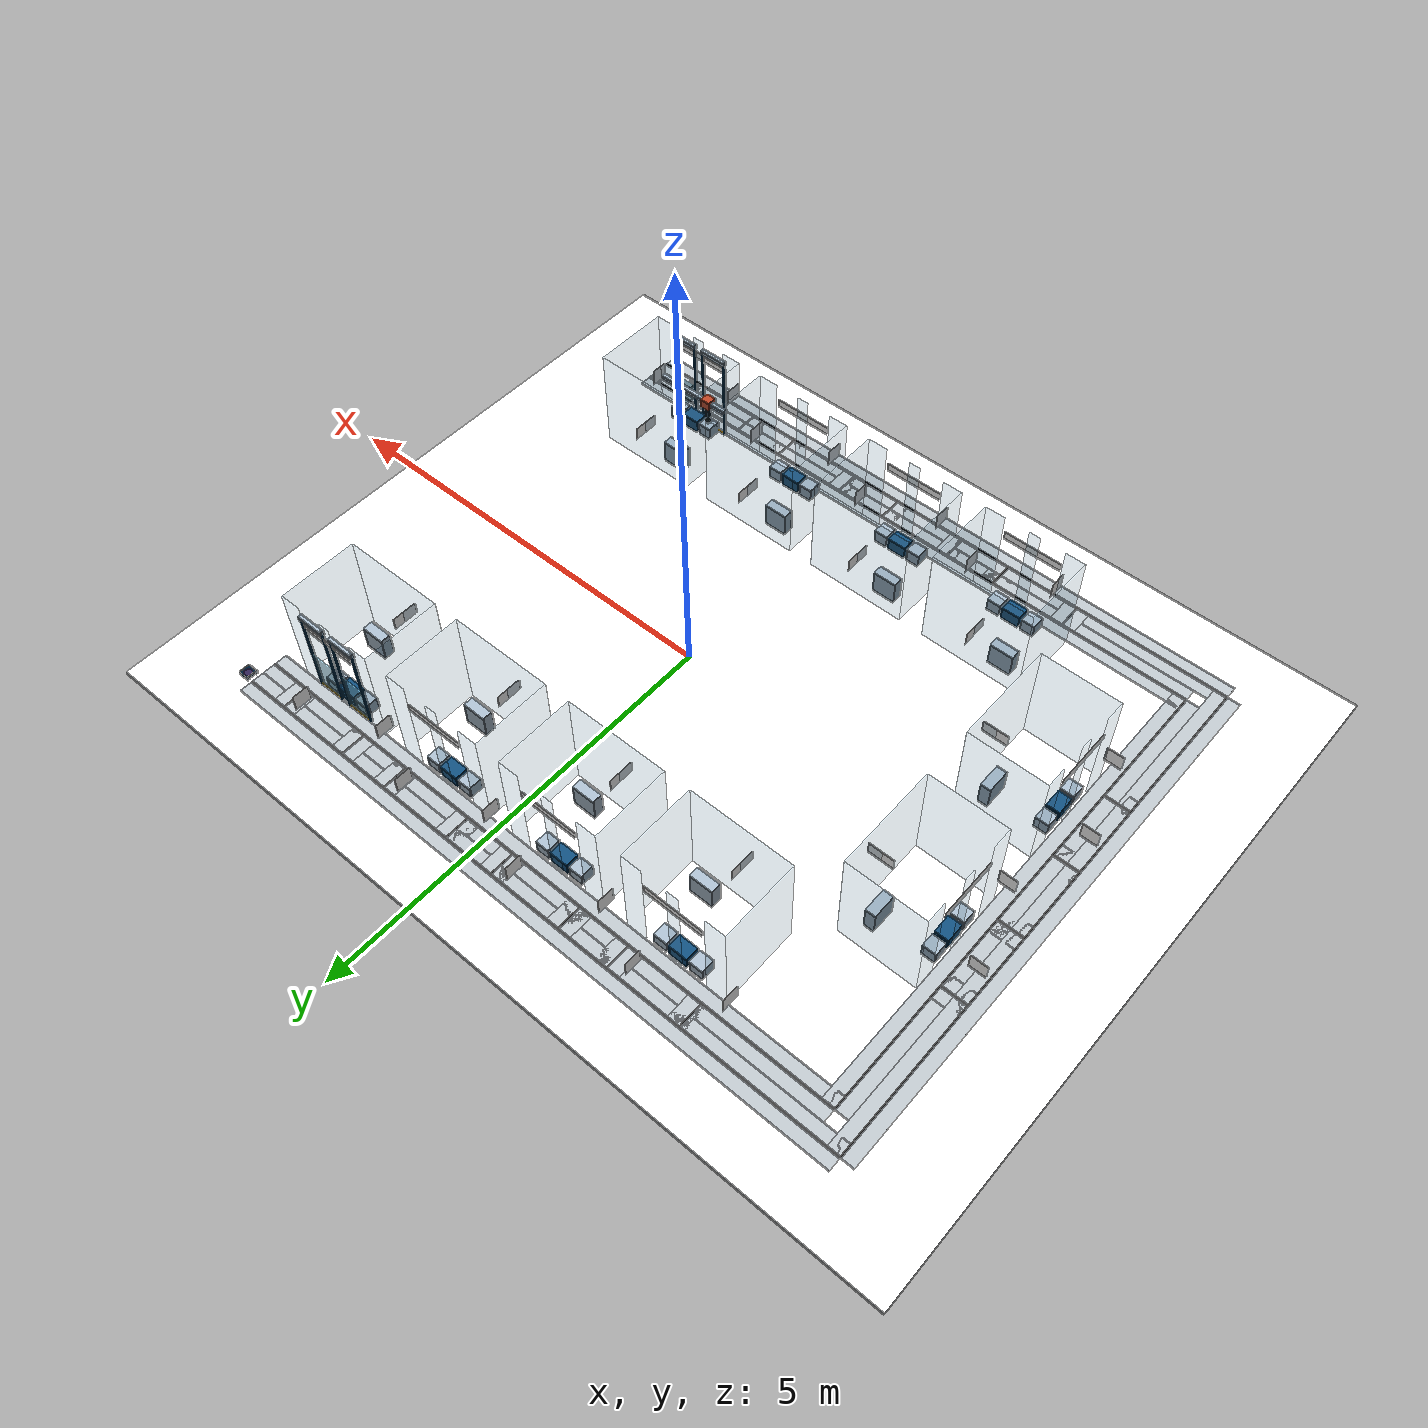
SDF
<sdf version="1.9">
 <world name="wafer_transport">
  <physics name="physics" type="ignored">
   <max_step_size>0.001</max_step_size>
   <real_time_factor>1.0</real_time_factor>
  </physics>
  <gravity>0 0 -9.81</gravity>
  <plugin filename="gz-sim-physics-system" name="gz::sim::systems::Physics"/>
  <plugin filename="gz-sim-user-commands-system" name="gz::sim::systems::UserCommands"/>
  <plugin filename="gz-sim-scene-broadcaster-system" name="gz::sim::systems::SceneBroadcaster"/>
  <plugin filename="gz-sim-sensors-system" name="gz::sim::systems::Sensors">
   <render_engine>ogre2</render_engine>
  </plugin>
  <scene><ambient>.7 .7 .7 1</ambient><background>.78 .83 .88 1</background><shadows>false</shadows></scene>
  <light name="overhead" type="directional">
   <pose>0 0 4 0 0 0</pose>
   <diffuse>.9 .9 .9 1</diffuse>
   <direction>-.2 .1 -1</direction>
  </light>
  <model name="loop_floor">
   <static>true</static>
   <link name="structure">
    <inertial>
     <mass>0.1</mass>
     <inertia>
      <ixx>0.00016666666666666672</ixx>
      <iyy>0.00016666666666666672</iyy>
      <izz>0.00016666666666666672</izz>
      <ixy>0</ixy>
      <ixz>0</ixz>
      <iyz>0</iyz>
     </inertia>
    </inertial>
    <visual name="floor">
     <pose>-0.65 0.0 -0.015 0 0 0</pose>
     <geometry><box><size>10.0 8.0 0.03</size></box></geometry>
     <material><ambient>0.93 0.95 0.97 1</ambient><diffuse>0.93 0.95 0.97 1</diffuse></material>
    </visual>
    <collision name="floor_collision">
     <pose>-0.65 0.0 -0.015 0 0 0</pose>
     <geometry><box><size>10.0 8.0 0.03</size></box></geometry>
     <surface><friction><ode><mu>0.9</mu><mu2>0.9</mu2></ode></friction></surface>
    </collision>
    <visual name="corridor_0">
     <pose>-0.6672 3.2224 0.00015 0 0 3.141592653589793</pose>
     <geometry><box><size>7.8275999999999994 0.3048 0.0002</size></box></geometry>
     <material><ambient>.72 .75 .77 1</ambient><diffuse>.72 .75 .77 1</diffuse></material>
    </visual>
    <visual name="tape_0">
     <pose>-0.6672 3.2224 0.0003 0 0 3.141592653589793</pose>
     <geometry><box><size>7.8266 0.018 0.0005</size></box></geometry>
     <material><ambient>.005 .005 .005 1</ambient><diffuse>.005 .005 .005 1</diffuse></material>
    </visual>
    <visual name="corridor_1">
     <pose>-4.58 0.0 0.00015 0 0 -1.5707963267948966</pose>
     <geometry><box><size>6.4468 0.3048 0.0002</size></box></geometry>
     <material><ambient>.72 .75 .77 1</ambient><diffuse>.72 .75 .77 1</diffuse></material>
    </visual>
    <visual name="tape_1">
     <pose>-4.58 0.0 0.0003 0 0 -1.5707963267948966</pose>
     <geometry><box><size>6.4458 0.018 0.0005</size></box></geometry>
     <material><ambient>.005 .005 .005 1</ambient><diffuse>.005 .005 .005 1</diffuse></material>
    </visual>
    <visual name="corridor_2">
     <pose>-0.6672 -3.2224 0.00015 0 0 0.0</pose>
     <geometry><box><size>7.8275999999999994 0.3048 0.0002</size></box></geometry>
     <material><ambient>.72 .75 .77 1</ambient><diffuse>.72 .75 .77 1</diffuse></material>
    </visual>
    <visual name="tape_2">
     <pose>-0.6672 -3.2224 0.0003 0 0 0.0</pose>
     <geometry><box><size>7.8266 0.018 0.0005</size></box></geometry>
     <material><ambient>.005 .005 .005 1</ambient><diffuse>.005 .005 .005 1</diffuse></material>
    </visual>
    <visual name="corridor_3">
     <pose>-0.5147999999999999 2.9175999999999997 0.00015 0 0 3.141592653589793</pose>
     <geometry><box><size>7.522799999999999 0.3048 0.0002</size></box></geometry>
     <material><ambient>.72 .75 .77 1</ambient><diffuse>.72 .75 .77 1</diffuse></material>
    </visual>
    <visual name="tape_3">
     <pose>-0.5147999999999999 2.9175999999999997 0.0003 0 0 3.141592653589793</pose>
     <geometry><box><size>7.5218 0.018 0.0005</size></box></geometry>
     <material><ambient>.005 .005 .005 1</ambient><diffuse>.005 .005 .005 1</diffuse></material>
    </visual>
    <visual name="corridor_4">
     <pose>-4.2752 0.0 0.00015 0 0 -1.5707963267948966</pose>
     <geometry><box><size>5.837199999999999 0.3048 0.0002</size></box></geometry>
     <material><ambient>.72 .75 .77 1</ambient><diffuse>.72 .75 .77 1</diffuse></material>
    </visual>
    <visual name="tape_4">
     <pose>-4.2752 0.0 0.0003 0 0 -1.5707963267948966</pose>
     <geometry><box><size>5.8362 0.018 0.0005</size></box></geometry>
     <material><ambient>.005 .005 .005 1</ambient><diffuse>.005 .005 .005 1</diffuse></material>
    </visual>
    <visual name="corridor_5">
     <pose>-0.5147999999999999 -2.9175999999999997 0.00015 0 0 0.0</pose>
     <geometry><box><size>7.522799999999999 0.3048 0.0002</size></box></geometry>
     <material><ambient>.72 .75 .77 1</ambient><diffuse>.72 .75 .77 1</diffuse></material>
    </visual>
    <visual name="tape_5">
     <pose>-0.5147999999999999 -2.9175999999999997 0.0003 0 0 0.0</pose>
     <geometry><box><size>7.5218 0.018 0.0005</size></box></geometry>
     <material><ambient>.005 .005 .005 1</ambient><diffuse>.005 .005 .005 1</diffuse></material>
    </visual>
    <visual name="corridor_6">
     <pose>2.736 3.07 0.00015 0 0 -1.5707963267948966</pose>
     <geometry><box><size>0.3068000000000002 0.3048 0.0002</size></box></geometry>
     <material><ambient>.72 .75 .77 1</ambient><diffuse>.72 .75 .77 1</diffuse></material>
    </visual>
    <visual name="tape_6">
     <pose>2.736 3.07 0.0003 0 0 -1.5707963267948966</pose>
     <geometry><box><size>0.3058000000000002 0.018 0.0005</size></box></geometry>
     <material><ambient>.005 .005 .005 1</ambient><diffuse>.005 .005 .005 1</diffuse></material>
    </visual>
    <visual name="corridor_7">
     <pose>1.2120000000000002 3.07 0.00015 0 0 -1.5707963267948974</pose>
     <geometry><box><size>0.3068000000000002 0.3048 0.0002</size></box></geometry>
     <material><ambient>.72 .75 .77 1</ambient><diffuse>.72 .75 .77 1</diffuse></material>
    </visual>
    <visual name="tape_7">
     <pose>1.2120000000000002 3.07 0.0003 0 0 -1.5707963267948974</pose>
     <geometry><box><size>0.3058000000000002 0.018 0.0005</size></box></geometry>
     <material><ambient>.005 .005 .005 1</ambient><diffuse>.005 .005 .005 1</diffuse></material>
    </visual>
    <visual name="corridor_8">
     <pose>-0.31199999999999994 3.07 0.00015 0 0 -1.5707963267948968</pose>
     <geometry><box><size>0.3068000000000002 0.3048 0.0002</size></box></geometry>
     <material><ambient>.72 .75 .77 1</ambient><diffuse>.72 .75 .77 1</diffuse></material>
    </visual>
    <visual name="tape_8">
     <pose>-0.31199999999999994 3.07 0.0003 0 0 -1.5707963267948968</pose>
     <geometry><box><size>0.3058000000000002 0.018 0.0005</size></box></geometry>
     <material><ambient>.005 .005 .005 1</ambient><diffuse>.005 .005 .005 1</diffuse></material>
    </visual>
    <visual name="corridor_9">
     <pose>-1.8359999999999999 3.07 0.00015 0 0 -1.5707963267948974</pose>
     <geometry><box><size>0.3068000000000002 0.3048 0.0002</size></box></geometry>
     <material><ambient>.72 .75 .77 1</ambient><diffuse>.72 .75 .77 1</diffuse></material>
    </visual>
    <visual name="tape_9">
     <pose>-1.8359999999999999 3.07 0.0003 0 0 -1.5707963267948974</pose>
     <geometry><box><size>0.3058000000000002 0.018 0.0005</size></box></geometry>
     <material><ambient>.005 .005 .005 1</ambient><diffuse>.005 .005 .005 1</diffuse></material>
    </visual>
    <visual name="corridor_10">
     <pose>-4.4276 1.3644 0.00015 0 0 0.0</pose>
     <geometry><box><size>0.3068000000000002 0.3048 0.0002</size></box></geometry>
     <material><ambient>.72 .75 .77 1</ambient><diffuse>.72 .75 .77 1</diffuse></material>
    </visual>
    <visual name="tape_10">
     <pose>-4.4276 1.3644 0.0003 0 0 0.0</pose>
     <geometry><box><size>0.3058000000000002 0.018 0.0005</size></box></geometry>
     <material><ambient>.005 .005 .005 1</ambient><diffuse>.005 .005 .005 1</diffuse></material>
    </visual>
    <visual name="corridor_11">
     <pose>-4.4276 -0.46440000000000003 0.00015 0 0 0.0</pose>
     <geometry><box><size>0.3068000000000002 0.3048 0.0002</size></box></geometry>
     <material><ambient>.72 .75 .77 1</ambient><diffuse>.72 .75 .77 1</diffuse></material>
    </visual>
    <visual name="tape_11">
     <pose>-4.4276 -0.46440000000000003 0.0003 0 0 0.0</pose>
     <geometry><box><size>0.3058000000000002 0.018 0.0005</size></box></geometry>
     <material><ambient>.005 .005 .005 1</ambient><diffuse>.005 .005 .005 1</diffuse></material>
    </visual>
    <visual name="corridor_12">
     <pose>-2.736 -3.07 0.00015 0 0 1.5707963267948966</pose>
     <geometry><box><size>0.3068000000000002 0.3048 0.0002</size></box></geometry>
     <material><ambient>.72 .75 .77 1</ambient><diffuse>.72 .75 .77 1</diffuse></material>
    </visual>
    <visual name="tape_12">
     <pose>-2.736 -3.07 0.0003 0 0 1.5707963267948966</pose>
     <geometry><box><size>0.3058000000000002 0.018 0.0005</size></box></geometry>
     <material><ambient>.005 .005 .005 1</ambient><diffuse>.005 .005 .005 1</diffuse></material>
    </visual>
    <visual name="corridor_13">
     <pose>-1.212 -3.07 0.00015 0 0 1.5707963267948966</pose>
     <geometry><box><size>0.3068000000000002 0.3048 0.0002</size></box></geometry>
     <material><ambient>.72 .75 .77 1</ambient><diffuse>.72 .75 .77 1</diffuse></material>
    </visual>
    <visual name="tape_13">
     <pose>-1.212 -3.07 0.0003 0 0 1.5707963267948966</pose>
     <geometry><box><size>0.3058000000000002 0.018 0.0005</size></box></geometry>
     <material><ambient>.005 .005 .005 1</ambient><diffuse>.005 .005 .005 1</diffuse></material>
    </visual>
    <visual name="corridor_14">
     <pose>0.312 -3.07 0.00015 0 0 1.5707963267948966</pose>
     <geometry><box><size>0.3068000000000002 0.3048 0.0002</size></box></geometry>
     <material><ambient>.72 .75 .77 1</ambient><diffuse>.72 .75 .77 1</diffuse></material>
    </visual>
    <visual name="tape_14">
     <pose>0.312 -3.07 0.0003 0 0 1.5707963267948966</pose>
     <geometry><box><size>0.3058000000000002 0.018 0.0005</size></box></geometry>
     <material><ambient>.005 .005 .005 1</ambient><diffuse>.005 .005 .005 1</diffuse></material>
    </visual>
    <visual name="corridor_15">
     <pose>1.836 -3.07 0.00015 0 0 1.5707963267948966</pose>
     <geometry><box><size>0.3068000000000002 0.3048 0.0002</size></box></geometry>
     <material><ambient>.72 .75 .77 1</ambient><diffuse>.72 .75 .77 1</diffuse></material>
    </visual>
    <visual name="tape_15">
     <pose>1.836 -3.07 0.0003 0 0 1.5707963267948966</pose>
     <geometry><box><size>0.3058000000000002 0.018 0.0005</size></box></geometry>
     <material><ambient>.005 .005 .005 1</ambient><diffuse>.005 .005 .005 1</diffuse></material>
    </visual>
    <visual name="corridor_16">
     <pose>1.8360000000000003 3.07 0.00015 0 0 1.570796326794896</pose>
     <geometry><box><size>0.3068000000000002 0.3048 0.0002</size></box></geometry>
     <material><ambient>.72 .75 .77 1</ambient><diffuse>.72 .75 .77 1</diffuse></material>
    </visual>
    <visual name="tape_16">
     <pose>1.8360000000000003 3.07 0.0003 0 0 1.570796326794896</pose>
     <geometry><box><size>0.3058000000000002 0.018 0.0005</size></box></geometry>
     <material><ambient>.005 .005 .005 1</ambient><diffuse>.005 .005 .005 1</diffuse></material>
    </visual>
    <visual name="corridor_17">
     <pose>0.31200000000000006 3.07 0.00015 0 0 1.5707963267948963</pose>
     <geometry><box><size>0.3068000000000002 0.3048 0.0002</size></box></geometry>
     <material><ambient>.72 .75 .77 1</ambient><diffuse>.72 .75 .77 1</diffuse></material>
    </visual>
    <visual name="tape_17">
     <pose>0.31200000000000006 3.07 0.0003 0 0 1.5707963267948963</pose>
     <geometry><box><size>0.3058000000000002 0.018 0.0005</size></box></geometry>
     <material><ambient>.005 .005 .005 1</ambient><diffuse>.005 .005 .005 1</diffuse></material>
    </visual>
    <visual name="corridor_18">
     <pose>-1.2119999999999997 3.07 0.00015 0 0 1.570796326794896</pose>
     <geometry><box><size>0.3068000000000002 0.3048 0.0002</size></box></geometry>
     <material><ambient>.72 .75 .77 1</ambient><diffuse>.72 .75 .77 1</diffuse></material>
    </visual>
    <visual name="tape_18">
     <pose>-1.2119999999999997 3.07 0.0003 0 0 1.570796326794896</pose>
     <geometry><box><size>0.3058000000000002 0.018 0.0005</size></box></geometry>
     <material><ambient>.005 .005 .005 1</ambient><diffuse>.005 .005 .005 1</diffuse></material>
    </visual>
    <visual name="corridor_19">
     <pose>-2.736 3.07 0.00015 0 0 1.5707963267948966</pose>
     <geometry><box><size>0.3068000000000002 0.3048 0.0002</size></box></geometry>
     <material><ambient>.72 .75 .77 1</ambient><diffuse>.72 .75 .77 1</diffuse></material>
    </visual>
    <visual name="tape_19">
     <pose>-2.736 3.07 0.0003 0 0 1.5707963267948966</pose>
     <geometry><box><size>0.3058000000000002 0.018 0.0005</size></box></geometry>
     <material><ambient>.005 .005 .005 1</ambient><diffuse>.005 .005 .005 1</diffuse></material>
    </visual>
    <visual name="corridor_20">
     <pose>-4.4276 0.4643999999999999 0.00015 0 0 3.141592653589793</pose>
     <geometry><box><size>0.3068000000000002 0.3048 0.0002</size></box></geometry>
     <material><ambient>.72 .75 .77 1</ambient><diffuse>.72 .75 .77 1</diffuse></material>
    </visual>
    <visual name="tape_20">
     <pose>-4.4276 0.4643999999999999 0.0003 0 0 3.141592653589793</pose>
     <geometry><box><size>0.3058000000000002 0.018 0.0005</size></box></geometry>
     <material><ambient>.005 .005 .005 1</ambient><diffuse>.005 .005 .005 1</diffuse></material>
    </visual>
    <visual name="corridor_21">
     <pose>-4.4276 -1.3644 0.00015 0 0 3.141592653589793</pose>
     <geometry><box><size>0.3068000000000002 0.3048 0.0002</size></box></geometry>
     <material><ambient>.72 .75 .77 1</ambient><diffuse>.72 .75 .77 1</diffuse></material>
    </visual>
    <visual name="tape_21">
     <pose>-4.4276 -1.3644 0.0003 0 0 3.141592653589793</pose>
     <geometry><box><size>0.3058000000000002 0.018 0.0005</size></box></geometry>
     <material><ambient>.005 .005 .005 1</ambient><diffuse>.005 .005 .005 1</diffuse></material>
    </visual>
    <visual name="corridor_22">
     <pose>-1.836 -3.07 0.00015 0 0 -1.5707963267948966</pose>
     <geometry><box><size>0.3068000000000002 0.3048 0.0002</size></box></geometry>
     <material><ambient>.72 .75 .77 1</ambient><diffuse>.72 .75 .77 1</diffuse></material>
    </visual>
    <visual name="tape_22">
     <pose>-1.836 -3.07 0.0003 0 0 -1.5707963267948966</pose>
     <geometry><box><size>0.3058000000000002 0.018 0.0005</size></box></geometry>
     <material><ambient>.005 .005 .005 1</ambient><diffuse>.005 .005 .005 1</diffuse></material>
    </visual>
    <visual name="corridor_23">
     <pose>-0.312 -3.07 0.00015 0 0 -1.5707963267948966</pose>
     <geometry><box><size>0.3068000000000002 0.3048 0.0002</size></box></geometry>
     <material><ambient>.72 .75 .77 1</ambient><diffuse>.72 .75 .77 1</diffuse></material>
    </visual>
    <visual name="tape_23">
     <pose>-0.312 -3.07 0.0003 0 0 -1.5707963267948966</pose>
     <geometry><box><size>0.3058000000000002 0.018 0.0005</size></box></geometry>
     <material><ambient>.005 .005 .005 1</ambient><diffuse>.005 .005 .005 1</diffuse></material>
    </visual>
    <visual name="corridor_24">
     <pose>1.212 -3.07 0.00015 0 0 -1.5707963267948966</pose>
     <geometry><box><size>0.3068000000000002 0.3048 0.0002</size></box></geometry>
     <material><ambient>.72 .75 .77 1</ambient><diffuse>.72 .75 .77 1</diffuse></material>
    </visual>
    <visual name="tape_24">
     <pose>1.212 -3.07 0.0003 0 0 -1.5707963267948966</pose>
     <geometry><box><size>0.3058000000000002 0.018 0.0005</size></box></geometry>
     <material><ambient>.005 .005 .005 1</ambient><diffuse>.005 .005 .005 1</diffuse></material>
    </visual>
    <visual name="corridor_25">
     <pose>2.736 -3.07 0.00015 0 0 -1.5707963267948966</pose>
     <geometry><box><size>0.3068000000000002 0.3048 0.0002</size></box></geometry>
     <material><ambient>.72 .75 .77 1</ambient><diffuse>.72 .75 .77 1</diffuse></material>
    </visual>
    <visual name="tape_25">
     <pose>2.736 -3.07 0.0003 0 0 -1.5707963267948966</pose>
     <geometry><box><size>0.3058000000000002 0.018 0.0005</size></box></geometry>
     <material><ambient>.005 .005 .005 1</ambient><diffuse>.005 .005 .005 1</diffuse></material>
    </visual>
    <visual name="loading_rail_-0.054">
     <pose>3.2456 3.1684 0.142 0 0 0</pose>
     <geometry><box><size>0.15 0.016 0.008</size></box></geometry>
     <material><ambient>0.65 0.72 0.78 1</ambient><diffuse>0.65 0.72 0.78 1</diffuse></material>
    </visual>
    <collision name="loading_rail_-0.054_collision">
     <pose>3.2456 3.1684 0.142 0 0 0</pose>
     <geometry><box><size>0.15 0.016 0.008</size></box></geometry>
     <surface><friction><ode><mu>0.9</mu><mu2>0.9</mu2></ode></friction></surface>
    </collision>
    <visual name="loading_rail_0.054">
     <pose>3.2456 3.2763999999999998 0.142 0 0 0</pose>
     <geometry><box><size>0.15 0.016 0.008</size></box></geometry>
     <material><ambient>0.65 0.72 0.78 1</ambient><diffuse>0.65 0.72 0.78 1</diffuse></material>
    </visual>
    <collision name="loading_rail_0.054_collision">
     <pose>3.2456 3.2763999999999998 0.142 0 0 0</pose>
     <geometry><box><size>0.15 0.016 0.008</size></box></geometry>
     <surface><friction><ode><mu>0.9</mu><mu2>0.9</mu2></ode></friction></surface>
    </collision>
   </link>
  </model>
  <model name="room_1">
   <static>true</static>
   <link name="structure">
    <inertial>
     <mass>0.1</mass>
     <inertia>
      <ixx>0.00016666666666666672</ixx>
      <iyy>0.00016666666666666672</iyy>
      <izz>0.00016666666666666672</izz>
      <ixy>0</ixy>
      <ixz>0</ixz>
      <iyz>0</iyz>
     </inertia>
    </inertial>
    <visual name="glass_back">
     <pose>2.286 1.8427999999999998 0.6096 0 0 3.141592653589793</pose>
     <geometry><box><size>1.2192 0.012 1.2192</size></box></geometry>
     <material><ambient>.5 .75 .9 1</ambient><diffuse>.5 .75 .9 1</diffuse></material>
     <transparency>0.82</transparency>
    </visual>
    <collision name="glass_back_collision">
     <pose>2.286 1.8427999999999998 0.6096 0 0 3.141592653589793</pose>
     <geometry><box><size>1.2192 0.012 1.2192</size></box></geometry>
     <surface><friction><ode><mu>0.9</mu><mu2>0.9</mu2></ode></friction></surface>
    </collision>
    <visual name="glass_left">
     <pose>2.8956 2.3 0.6096 0 0 3.141592653589793</pose>
     <geometry><box><size>0.012 0.9144 1.2192</size></box></geometry>
     <material><ambient>.5 .75 .9 1</ambient><diffuse>.5 .75 .9 1</diffuse></material>
     <transparency>0.82</transparency>
    </visual>
    <collision name="glass_left_collision">
     <pose>2.8956 2.3 0.6096 0 0 3.141592653589793</pose>
     <geometry><box><size>0.012 0.9144 1.2192</size></box></geometry>
     <surface><friction><ode><mu>0.9</mu><mu2>0.9</mu2></ode></friction></surface>
    </collision>
    <visual name="glass_right">
     <pose>1.6764000000000001 2.3 0.6096 0 0 3.141592653589793</pose>
     <geometry><box><size>0.012 0.9144 1.2192</size></box></geometry>
     <material><ambient>.5 .75 .9 1</ambient><diffuse>.5 .75 .9 1</diffuse></material>
     <transparency>0.82</transparency>
    </visual>
    <collision name="glass_right_collision">
     <pose>1.6764000000000001 2.3 0.6096 0 0 3.141592653589793</pose>
     <geometry><box><size>0.012 0.9144 1.2192</size></box></geometry>
     <surface><friction><ode><mu>0.9</mu><mu2>0.9</mu2></ode></friction></surface>
    </collision>
    <visual name="glass_front_0">
     <pose>2.777 2.7571999999999997 0.6096 0 0 3.141592653589793</pose>
     <geometry><box><size>0.23720000000000002 0.012 1.2192</size></box></geometry>
     <material><ambient>.5 .75 .9 1</ambient><diffuse>.5 .75 .9 1</diffuse></material>
     <transparency>0.82</transparency>
    </visual>
    <collision name="glass_front_0_collision">
     <pose>2.777 2.7571999999999997 0.6096 0 0 3.141592653589793</pose>
     <geometry><box><size>0.23720000000000002 0.012 1.2192</size></box></geometry>
     <surface><friction><ode><mu>0.9</mu><mu2>0.9</mu2></ode></friction></surface>
    </collision>
    <visual name="glass_front_1">
     <pose>2.286 2.7571999999999997 0.6096 0 0 3.141592653589793</pose>
     <geometry><box><size>0.1352 0.012 1.2192</size></box></geometry>
     <material><ambient>.5 .75 .9 1</ambient><diffuse>.5 .75 .9 1</diffuse></material>
     <transparency>0.82</transparency>
    </visual>
    <collision name="glass_front_1_collision">
     <pose>2.286 2.7571999999999997 0.6096 0 0 3.141592653589793</pose>
     <geometry><box><size>0.1352 0.012 1.2192</size></box></geometry>
     <surface><friction><ode><mu>0.9</mu><mu2>0.9</mu2></ode></friction></surface>
    </collision>
    <visual name="glass_front_2">
     <pose>1.795 2.7571999999999997 0.6096 0 0 3.141592653589793</pose>
     <geometry><box><size>0.23720000000000002 0.012 1.2192</size></box></geometry>
     <material><ambient>.5 .75 .9 1</ambient><diffuse>.5 .75 .9 1</diffuse></material>
     <transparency>0.82</transparency>
    </visual>
    <collision name="glass_front_2_collision">
     <pose>1.795 2.7571999999999997 0.6096 0 0 3.141592653589793</pose>
     <geometry><box><size>0.23720000000000002 0.012 1.2192</size></box></geometry>
     <surface><friction><ode><mu>0.9</mu><mu2>0.9</mu2></ode></friction></surface>
    </collision>
    <visual name="process_stage">
     <pose>2.286 2.6571999999999996 0.077 0 0 3.141592653589793</pose>
     <geometry><box><size>0.22 0.16 0.154</size></box></geometry>
     <material><ambient>0.06 0.30 0.48 1</ambient><diffuse>0.06 0.30 0.48 1</diffuse></material>
    </visual>
    <collision name="process_stage_collision">
     <pose>2.286 2.6571999999999996 0.077 0 0 3.141592653589793</pose>
     <geometry><box><size>0.22 0.16 0.154</size></box></geometry>
     <surface><friction><ode><mu>0.9</mu><mu2>0.9</mu2></ode></friction></surface>
    </collision>
    <visual name="entry_handoff">
     <pose>2.5060000000000002 2.6571999999999996 0.077 0 0 3.141592653589793</pose>
     <geometry><box><size>0.16 0.16 0.154</size></box></geometry>
     <material><ambient>0.65 0.72 0.78 1</ambient><diffuse>0.65 0.72 0.78 1</diffuse></material>
    </visual>
    <collision name="entry_handoff_collision">
     <pose>2.5060000000000002 2.6571999999999996 0.077 0 0 3.141592653589793</pose>
     <geometry><box><size>0.16 0.16 0.154</size></box></geometry>
     <surface><friction><ode><mu>0.9</mu><mu2>0.9</mu2></ode></friction></surface>
    </collision>
    <visual name="exit_handoff">
     <pose>2.066 2.6571999999999996 0.077 0 0 3.141592653589793</pose>
     <geometry><box><size>0.16 0.16 0.154</size></box></geometry>
     <material><ambient>0.65 0.72 0.78 1</ambient><diffuse>0.65 0.72 0.78 1</diffuse></material>
    </visual>
    <collision name="exit_handoff_collision">
     <pose>2.066 2.6571999999999996 0.077 0 0 3.141592653589793</pose>
     <geometry><box><size>0.16 0.16 0.154</size></box></geometry>
     <surface><friction><ode><mu>0.9</mu><mu2>0.9</mu2></ode></friction></surface>
    </collision>
    <visual name="equipment">
     <pose>2.556 2.05 0.14 0 0 3.141592653589793</pose>
     <geometry><box><size>0.28 0.12 0.28</size></box></geometry>
     <material><ambient>0.65 0.72 0.78 1</ambient><diffuse>0.65 0.72 0.78 1</diffuse></material>
    </visual>
    <collision name="equipment_collision">
     <pose>2.556 2.05 0.14 0 0 3.141592653589793</pose>
     <geometry><box><size>0.28 0.12 0.28</size></box></geometry>
     <surface><friction><ode><mu>0.9</mu><mu2>0.9</mu2></ode></friction></surface>
    </collision>
    <visual name="entry_apriltag">
     <pose>2.486 3.1174 0.27 1.5707963267948966 0 7.853981633974483</pose>
     <geometry><plane><normal>0 0 1</normal><size>0.2 0.2</size></plane></geometry>
     <material>
      <ambient>1 1 1 1</ambient>
      <diffuse>1 1 1 1</diffuse>
      <emissive>0.35 0.35 0.35 1</emissive>
      <pbr>
       <metal>
        <albedo_map>../textures/room_1_entry_apriltag.png</albedo_map>
        <metalness>0</metalness>
        <roughness>1</roughness>
       </metal>
      </pbr>
     </material>
     <cast_shadows>false</cast_shadows>
    </visual>
    <visual name="exit_apriltag">
     <pose>1.586 2.8125999999999998 0.27 1.5707963267948966 0 7.853981633974483</pose>
     <geometry><plane><normal>0 0 1</normal><size>0.2 0.2</size></plane></geometry>
     <material>
      <ambient>1 1 1 1</ambient>
      <diffuse>1 1 1 1</diffuse>
      <emissive>0.35 0.35 0.35 1</emissive>
      <pbr>
       <metal>
        <albedo_map>../textures/room_1_exit_apriltag.png</albedo_map>
        <metalness>0</metalness>
        <roughness>1</roughness>
       </metal>
      </pbr>
     </material>
     <cast_shadows>false</cast_shadows>
    </visual>
    <visual name="room_label">
     <pose>2.286 2.7662 0.98 1.5707963267948966 0 3.141592653589793</pose>
     <geometry><plane><normal>0 0 1</normal><size>0.7 0.1</size></plane></geometry>
     <material>
      <ambient>1 1 1 1</ambient>
      <diffuse>1 1 1 1</diffuse>
      <emissive>0.35 0.35 0.35 1</emissive>
      <pbr>
       <metal>
        <albedo_map>../textures/room_1_label.png</albedo_map>
        <metalness>0</metalness>
        <roughness>1</roughness>
       </metal>
      </pbr>
     </material>
     <cast_shadows>false</cast_shadows>
    </visual>
    <visual name="microalchemy_logo">
     <pose>2.286 1.8327999999999998 0.55 1.5707963267948966 0 4.71238898038469</pose>
     <geometry><plane><normal>0 0 1</normal><size>0.3 0.15</size></plane></geometry>
     <material>
      <ambient>1 1 1 1</ambient>
      <diffuse>1 1 1 1</diffuse>
      <emissive>0.35 0.35 0.35 1</emissive>
      <pbr>
       <metal>
        <albedo_map>../textures/microalchemy_logo.png</albedo_map>
        <metalness>0</metalness>
        <roughness>1</roughness>
       </metal>
      </pbr>
     </material>
     <cast_shadows>false</cast_shadows>
    </visual>
   </link>
  </model>
  <include>
   <uri>model://room_1_entry_door</uri>
   <name>room_1_entry_door</name>
   <pose>2.3386000000000005 2.7571999999999997 0.0 0 0 4.71238898038469</pose>
  </include>
  <include>
   <uri>model://room_1_exit_door</uri>
   <name>room_1_exit_door</name>
   <pose>1.8985999999999998 2.7571999999999997 0.0 0 0 4.71238898038469</pose>
  </include>
  <model name="room_2">
   <static>true</static>
   <link name="structure">
    <inertial>
     <mass>0.1</mass>
     <inertia>
      <ixx>0.00016666666666666672</ixx>
      <iyy>0.00016666666666666672</iyy>
      <izz>0.00016666666666666672</izz>
      <ixy>0</ixy>
      <ixz>0</ixz>
      <iyz>0</iyz>
     </inertia>
    </inertial>
    <visual name="glass_back">
     <pose>0.7619999999999999 1.8427999999999998 0.6096 0 0 3.141592653589793</pose>
     <geometry><box><size>1.2192 0.012 1.2192</size></box></geometry>
     <material><ambient>.5 .75 .9 1</ambient><diffuse>.5 .75 .9 1</diffuse></material>
     <transparency>0.82</transparency>
    </visual>
    <collision name="glass_back_collision">
     <pose>0.7619999999999999 1.8427999999999998 0.6096 0 0 3.141592653589793</pose>
     <geometry><box><size>1.2192 0.012 1.2192</size></box></geometry>
     <surface><friction><ode><mu>0.9</mu><mu2>0.9</mu2></ode></friction></surface>
    </collision>
    <visual name="glass_left">
     <pose>1.3716 2.3 0.6096 0 0 3.141592653589793</pose>
     <geometry><box><size>0.012 0.9144 1.2192</size></box></geometry>
     <material><ambient>.5 .75 .9 1</ambient><diffuse>.5 .75 .9 1</diffuse></material>
     <transparency>0.82</transparency>
    </visual>
    <collision name="glass_left_collision">
     <pose>1.3716 2.3 0.6096 0 0 3.141592653589793</pose>
     <geometry><box><size>0.012 0.9144 1.2192</size></box></geometry>
     <surface><friction><ode><mu>0.9</mu><mu2>0.9</mu2></ode></friction></surface>
    </collision>
    <visual name="glass_right">
     <pose>0.15239999999999998 2.3 0.6096 0 0 3.141592653589793</pose>
     <geometry><box><size>0.012 0.9144 1.2192</size></box></geometry>
     <material><ambient>.5 .75 .9 1</ambient><diffuse>.5 .75 .9 1</diffuse></material>
     <transparency>0.82</transparency>
    </visual>
    <collision name="glass_right_collision">
     <pose>0.15239999999999998 2.3 0.6096 0 0 3.141592653589793</pose>
     <geometry><box><size>0.012 0.9144 1.2192</size></box></geometry>
     <surface><friction><ode><mu>0.9</mu><mu2>0.9</mu2></ode></friction></surface>
    </collision>
    <visual name="glass_front_0">
     <pose>1.2530000000000001 2.7571999999999997 0.6096 0 0 3.141592653589793</pose>
     <geometry><box><size>0.23720000000000002 0.012 1.2192</size></box></geometry>
     <material><ambient>.5 .75 .9 1</ambient><diffuse>.5 .75 .9 1</diffuse></material>
     <transparency>0.82</transparency>
    </visual>
    <collision name="glass_front_0_collision">
     <pose>1.2530000000000001 2.7571999999999997 0.6096 0 0 3.141592653589793</pose>
     <geometry><box><size>0.23720000000000002 0.012 1.2192</size></box></geometry>
     <surface><friction><ode><mu>0.9</mu><mu2>0.9</mu2></ode></friction></surface>
    </collision>
    <visual name="glass_front_1">
     <pose>0.7620000000000001 2.7571999999999997 0.6096 0 0 3.141592653589793</pose>
     <geometry><box><size>0.1352 0.012 1.2192</size></box></geometry>
     <material><ambient>.5 .75 .9 1</ambient><diffuse>.5 .75 .9 1</diffuse></material>
     <transparency>0.82</transparency>
    </visual>
    <collision name="glass_front_1_collision">
     <pose>0.7620000000000001 2.7571999999999997 0.6096 0 0 3.141592653589793</pose>
     <geometry><box><size>0.1352 0.012 1.2192</size></box></geometry>
     <surface><friction><ode><mu>0.9</mu><mu2>0.9</mu2></ode></friction></surface>
    </collision>
    <visual name="glass_front_2">
     <pose>0.2710000000000001 2.7571999999999997 0.6096 0 0 3.141592653589793</pose>
     <geometry><box><size>0.23720000000000002 0.012 1.2192</size></box></geometry>
     <material><ambient>.5 .75 .9 1</ambient><diffuse>.5 .75 .9 1</diffuse></material>
     <transparency>0.82</transparency>
    </visual>
    <collision name="glass_front_2_collision">
     <pose>0.2710000000000001 2.7571999999999997 0.6096 0 0 3.141592653589793</pose>
     <geometry><box><size>0.23720000000000002 0.012 1.2192</size></box></geometry>
     <surface><friction><ode><mu>0.9</mu><mu2>0.9</mu2></ode></friction></surface>
    </collision>
    <visual name="process_stage">
     <pose>0.762 2.6571999999999996 0.077 0 0 3.141592653589793</pose>
     <geometry><box><size>0.22 0.16 0.154</size></box></geometry>
     <material><ambient>0.06 0.30 0.48 1</ambient><diffuse>0.06 0.30 0.48 1</diffuse></material>
    </visual>
    <collision name="process_stage_collision">
     <pose>0.762 2.6571999999999996 0.077 0 0 3.141592653589793</pose>
     <geometry><box><size>0.22 0.16 0.154</size></box></geometry>
     <surface><friction><ode><mu>0.9</mu><mu2>0.9</mu2></ode></friction></surface>
    </collision>
    <visual name="entry_handoff">
     <pose>0.982 2.6571999999999996 0.077 0 0 3.141592653589793</pose>
     <geometry><box><size>0.16 0.16 0.154</size></box></geometry>
     <material><ambient>0.65 0.72 0.78 1</ambient><diffuse>0.65 0.72 0.78 1</diffuse></material>
    </visual>
    <collision name="entry_handoff_collision">
     <pose>0.982 2.6571999999999996 0.077 0 0 3.141592653589793</pose>
     <geometry><box><size>0.16 0.16 0.154</size></box></geometry>
     <surface><friction><ode><mu>0.9</mu><mu2>0.9</mu2></ode></friction></surface>
    </collision>
    <visual name="exit_handoff">
     <pose>0.542 2.6571999999999996 0.077 0 0 3.141592653589793</pose>
     <geometry><box><size>0.16 0.16 0.154</size></box></geometry>
     <material><ambient>0.65 0.72 0.78 1</ambient><diffuse>0.65 0.72 0.78 1</diffuse></material>
    </visual>
    <collision name="exit_handoff_collision">
     <pose>0.542 2.6571999999999996 0.077 0 0 3.141592653589793</pose>
     <geometry><box><size>0.16 0.16 0.154</size></box></geometry>
     <surface><friction><ode><mu>0.9</mu><mu2>0.9</mu2></ode></friction></surface>
    </collision>
    <visual name="equipment">
     <pose>1.032 2.05 0.14 0 0 3.141592653589793</pose>
     <geometry><box><size>0.28 0.12 0.28</size></box></geometry>
     <material><ambient>0.65 0.72 0.78 1</ambient><diffuse>0.65 0.72 0.78 1</diffuse></material>
    </visual>
    <collision name="equipment_collision">
     <pose>1.032 2.05 0.14 0 0 3.141592653589793</pose>
     <geometry><box><size>0.28 0.12 0.28</size></box></geometry>
     <surface><friction><ode><mu>0.9</mu><mu2>0.9</mu2></ode></friction></surface>
    </collision>
    <visual name="entry_apriltag">
     <pose>0.9620000000000001 3.1174 0.27 1.5707963267948966 0 7.853981633974483</pose>
     <geometry><plane><normal>0 0 1</normal><size>0.2 0.2</size></plane></geometry>
     <material>
      <ambient>1 1 1 1</ambient>
      <diffuse>1 1 1 1</diffuse>
      <emissive>0.35 0.35 0.35 1</emissive>
      <pbr>
       <metal>
        <albedo_map>../textures/room_2_entry_apriltag.png</albedo_map>
        <metalness>0</metalness>
        <roughness>1</roughness>
       </metal>
      </pbr>
     </material>
     <cast_shadows>false</cast_shadows>
    </visual>
    <visual name="exit_apriltag">
     <pose>0.06200000000000012 2.8125999999999998 0.27 1.5707963267948966 0 7.853981633974483</pose>
     <geometry><plane><normal>0 0 1</normal><size>0.2 0.2</size></plane></geometry>
     <material>
      <ambient>1 1 1 1</ambient>
      <diffuse>1 1 1 1</diffuse>
      <emissive>0.35 0.35 0.35 1</emissive>
      <pbr>
       <metal>
        <albedo_map>../textures/room_2_exit_apriltag.png</albedo_map>
        <metalness>0</metalness>
        <roughness>1</roughness>
       </metal>
      </pbr>
     </material>
     <cast_shadows>false</cast_shadows>
    </visual>
    <visual name="room_label">
     <pose>0.7620000000000001 2.7662 0.98 1.5707963267948966 0 3.141592653589793</pose>
     <geometry><plane><normal>0 0 1</normal><size>0.7 0.1</size></plane></geometry>
     <material>
      <ambient>1 1 1 1</ambient>
      <diffuse>1 1 1 1</diffuse>
      <emissive>0.35 0.35 0.35 1</emissive>
      <pbr>
       <metal>
        <albedo_map>../textures/room_2_label.png</albedo_map>
        <metalness>0</metalness>
        <roughness>1</roughness>
       </metal>
      </pbr>
     </material>
     <cast_shadows>false</cast_shadows>
    </visual>
    <visual name="microalchemy_logo">
     <pose>0.7619999999999999 1.8327999999999998 0.55 1.5707963267948966 0 4.71238898038469</pose>
     <geometry><plane><normal>0 0 1</normal><size>0.3 0.15</size></plane></geometry>
     <material>
      <ambient>1 1 1 1</ambient>
      <diffuse>1 1 1 1</diffuse>
      <emissive>0.35 0.35 0.35 1</emissive>
      <pbr>
       <metal>
        <albedo_map>../textures/microalchemy_logo.png</albedo_map>
        <metalness>0</metalness>
        <roughness>1</roughness>
       </metal>
      </pbr>
     </material>
     <cast_shadows>false</cast_shadows>
    </visual>
   </link>
  </model>
  <model name="room_3">
   <static>true</static>
   <link name="structure">
    <inertial>
     <mass>0.1</mass>
     <inertia>
      <ixx>0.00016666666666666672</ixx>
      <iyy>0.00016666666666666672</iyy>
      <izz>0.00016666666666666672</izz>
      <ixy>0</ixy>
      <ixz>0</ixz>
      <iyz>0</iyz>
     </inertia>
    </inertial>
    <visual name="glass_back">
     <pose>-0.7620000000000001 1.8427999999999998 0.6096 0 0 3.141592653589793</pose>
     <geometry><box><size>1.2192 0.012 1.2192</size></box></geometry>
     <material><ambient>.5 .75 .9 1</ambient><diffuse>.5 .75 .9 1</diffuse></material>
     <transparency>0.82</transparency>
    </visual>
    <collision name="glass_back_collision">
     <pose>-0.7620000000000001 1.8427999999999998 0.6096 0 0 3.141592653589793</pose>
     <geometry><box><size>1.2192 0.012 1.2192</size></box></geometry>
     <surface><friction><ode><mu>0.9</mu><mu2>0.9</mu2></ode></friction></surface>
    </collision>
    <visual name="glass_left">
     <pose>-0.15239999999999998 2.3 0.6096 0 0 3.141592653589793</pose>
     <geometry><box><size>0.012 0.9144 1.2192</size></box></geometry>
     <material><ambient>.5 .75 .9 1</ambient><diffuse>.5 .75 .9 1</diffuse></material>
     <transparency>0.82</transparency>
    </visual>
    <collision name="glass_left_collision">
     <pose>-0.15239999999999998 2.3 0.6096 0 0 3.141592653589793</pose>
     <geometry><box><size>0.012 0.9144 1.2192</size></box></geometry>
     <surface><friction><ode><mu>0.9</mu><mu2>0.9</mu2></ode></friction></surface>
    </collision>
    <visual name="glass_right">
     <pose>-1.3716 2.3 0.6096 0 0 3.141592653589793</pose>
     <geometry><box><size>0.012 0.9144 1.2192</size></box></geometry>
     <material><ambient>.5 .75 .9 1</ambient><diffuse>.5 .75 .9 1</diffuse></material>
     <transparency>0.82</transparency>
    </visual>
    <collision name="glass_right_collision">
     <pose>-1.3716 2.3 0.6096 0 0 3.141592653589793</pose>
     <geometry><box><size>0.012 0.9144 1.2192</size></box></geometry>
     <surface><friction><ode><mu>0.9</mu><mu2>0.9</mu2></ode></friction></surface>
    </collision>
    <visual name="glass_front_0">
     <pose>-0.27099999999999996 2.7571999999999997 0.6096 0 0 3.141592653589793</pose>
     <geometry><box><size>0.23720000000000002 0.012 1.2192</size></box></geometry>
     <material><ambient>.5 .75 .9 1</ambient><diffuse>.5 .75 .9 1</diffuse></material>
     <transparency>0.82</transparency>
    </visual>
    <collision name="glass_front_0_collision">
     <pose>-0.27099999999999996 2.7571999999999997 0.6096 0 0 3.141592653589793</pose>
     <geometry><box><size>0.23720000000000002 0.012 1.2192</size></box></geometry>
     <surface><friction><ode><mu>0.9</mu><mu2>0.9</mu2></ode></friction></surface>
    </collision>
    <visual name="glass_front_1">
     <pose>-0.7619999999999999 2.7571999999999997 0.6096 0 0 3.141592653589793</pose>
     <geometry><box><size>0.1352 0.012 1.2192</size></box></geometry>
     <material><ambient>.5 .75 .9 1</ambient><diffuse>.5 .75 .9 1</diffuse></material>
     <transparency>0.82</transparency>
    </visual>
    <collision name="glass_front_1_collision">
     <pose>-0.7619999999999999 2.7571999999999997 0.6096 0 0 3.141592653589793</pose>
     <geometry><box><size>0.1352 0.012 1.2192</size></box></geometry>
     <surface><friction><ode><mu>0.9</mu><mu2>0.9</mu2></ode></friction></surface>
    </collision>
    <visual name="glass_front_2">
     <pose>-1.2530000000000001 2.7571999999999997 0.6096 0 0 3.141592653589793</pose>
     <geometry><box><size>0.23720000000000002 0.012 1.2192</size></box></geometry>
     <material><ambient>.5 .75 .9 1</ambient><diffuse>.5 .75 .9 1</diffuse></material>
     <transparency>0.82</transparency>
    </visual>
    <collision name="glass_front_2_collision">
     <pose>-1.2530000000000001 2.7571999999999997 0.6096 0 0 3.141592653589793</pose>
     <geometry><box><size>0.23720000000000002 0.012 1.2192</size></box></geometry>
     <surface><friction><ode><mu>0.9</mu><mu2>0.9</mu2></ode></friction></surface>
    </collision>
    <visual name="process_stage">
     <pose>-0.762 2.6571999999999996 0.077 0 0 3.141592653589793</pose>
     <geometry><box><size>0.22 0.16 0.154</size></box></geometry>
     <material><ambient>0.06 0.30 0.48 1</ambient><diffuse>0.06 0.30 0.48 1</diffuse></material>
    </visual>
    <collision name="process_stage_collision">
     <pose>-0.762 2.6571999999999996 0.077 0 0 3.141592653589793</pose>
     <geometry><box><size>0.22 0.16 0.154</size></box></geometry>
     <surface><friction><ode><mu>0.9</mu><mu2>0.9</mu2></ode></friction></surface>
    </collision>
    <visual name="entry_handoff">
     <pose>-0.542 2.6571999999999996 0.077 0 0 3.141592653589793</pose>
     <geometry><box><size>0.16 0.16 0.154</size></box></geometry>
     <material><ambient>0.65 0.72 0.78 1</ambient><diffuse>0.65 0.72 0.78 1</diffuse></material>
    </visual>
    <collision name="entry_handoff_collision">
     <pose>-0.542 2.6571999999999996 0.077 0 0 3.141592653589793</pose>
     <geometry><box><size>0.16 0.16 0.154</size></box></geometry>
     <surface><friction><ode><mu>0.9</mu><mu2>0.9</mu2></ode></friction></surface>
    </collision>
    <visual name="exit_handoff">
     <pose>-0.982 2.6571999999999996 0.077 0 0 3.141592653589793</pose>
     <geometry><box><size>0.16 0.16 0.154</size></box></geometry>
     <material><ambient>0.65 0.72 0.78 1</ambient><diffuse>0.65 0.72 0.78 1</diffuse></material>
    </visual>
    <collision name="exit_handoff_collision">
     <pose>-0.982 2.6571999999999996 0.077 0 0 3.141592653589793</pose>
     <geometry><box><size>0.16 0.16 0.154</size></box></geometry>
     <surface><friction><ode><mu>0.9</mu><mu2>0.9</mu2></ode></friction></surface>
    </collision>
    <visual name="equipment">
     <pose>-0.49200000000000005 2.05 0.14 0 0 3.141592653589793</pose>
     <geometry><box><size>0.28 0.12 0.28</size></box></geometry>
     <material><ambient>0.65 0.72 0.78 1</ambient><diffuse>0.65 0.72 0.78 1</diffuse></material>
    </visual>
    <collision name="equipment_collision">
     <pose>-0.49200000000000005 2.05 0.14 0 0 3.141592653589793</pose>
     <geometry><box><size>0.28 0.12 0.28</size></box></geometry>
     <surface><friction><ode><mu>0.9</mu><mu2>0.9</mu2></ode></friction></surface>
    </collision>
    <visual name="entry_apriltag">
     <pose>-0.5619999999999999 3.1174 0.27 1.5707963267948966 0 7.853981633974483</pose>
     <geometry><plane><normal>0 0 1</normal><size>0.2 0.2</size></plane></geometry>
     <material>
      <ambient>1 1 1 1</ambient>
      <diffuse>1 1 1 1</diffuse>
      <emissive>0.35 0.35 0.35 1</emissive>
      <pbr>
       <metal>
        <albedo_map>../textures/room_3_entry_apriltag.png</albedo_map>
        <metalness>0</metalness>
        <roughness>1</roughness>
       </metal>
      </pbr>
     </material>
     <cast_shadows>false</cast_shadows>
    </visual>
    <visual name="exit_apriltag">
     <pose>-1.462 2.8125999999999998 0.27 1.5707963267948966 0 7.853981633974483</pose>
     <geometry><plane><normal>0 0 1</normal><size>0.2 0.2</size></plane></geometry>
     <material>
      <ambient>1 1 1 1</ambient>
      <diffuse>1 1 1 1</diffuse>
      <emissive>0.35 0.35 0.35 1</emissive>
      <pbr>
       <metal>
        <albedo_map>../textures/room_3_exit_apriltag.png</albedo_map>
        <metalness>0</metalness>
        <roughness>1</roughness>
       </metal>
      </pbr>
     </material>
     <cast_shadows>false</cast_shadows>
    </visual>
    <visual name="room_label">
     <pose>-0.7619999999999999 2.7662 0.98 1.5707963267948966 0 3.141592653589793</pose>
     <geometry><plane><normal>0 0 1</normal><size>0.7 0.1</size></plane></geometry>
     <material>
      <ambient>1 1 1 1</ambient>
      <diffuse>1 1 1 1</diffuse>
      <emissive>0.35 0.35 0.35 1</emissive>
      <pbr>
       <metal>
        <albedo_map>../textures/room_3_label.png</albedo_map>
        <metalness>0</metalness>
        <roughness>1</roughness>
       </metal>
      </pbr>
     </material>
     <cast_shadows>false</cast_shadows>
    </visual>
    <visual name="microalchemy_logo">
     <pose>-0.7620000000000001 1.8327999999999998 0.55 1.5707963267948966 0 4.71238898038469</pose>
     <geometry><plane><normal>0 0 1</normal><size>0.3 0.15</size></plane></geometry>
     <material>
      <ambient>1 1 1 1</ambient>
      <diffuse>1 1 1 1</diffuse>
      <emissive>0.35 0.35 0.35 1</emissive>
      <pbr>
       <metal>
        <albedo_map>../textures/microalchemy_logo.png</albedo_map>
        <metalness>0</metalness>
        <roughness>1</roughness>
       </metal>
      </pbr>
     </material>
     <cast_shadows>false</cast_shadows>
    </visual>
   </link>
  </model>
  <model name="room_4">
   <static>true</static>
   <link name="structure">
    <inertial>
     <mass>0.1</mass>
     <inertia>
      <ixx>0.00016666666666666672</ixx>
      <iyy>0.00016666666666666672</iyy>
      <izz>0.00016666666666666672</izz>
      <ixy>0</ixy>
      <ixz>0</ixz>
      <iyz>0</iyz>
     </inertia>
    </inertial>
    <visual name="glass_back">
     <pose>-2.286 1.8427999999999998 0.6096 0 0 3.141592653589793</pose>
     <geometry><box><size>1.2192 0.012 1.2192</size></box></geometry>
     <material><ambient>.5 .75 .9 1</ambient><diffuse>.5 .75 .9 1</diffuse></material>
     <transparency>0.82</transparency>
    </visual>
    <collision name="glass_back_collision">
     <pose>-2.286 1.8427999999999998 0.6096 0 0 3.141592653589793</pose>
     <geometry><box><size>1.2192 0.012 1.2192</size></box></geometry>
     <surface><friction><ode><mu>0.9</mu><mu2>0.9</mu2></ode></friction></surface>
    </collision>
    <visual name="glass_left">
     <pose>-1.6764000000000001 2.3 0.6096 0 0 3.141592653589793</pose>
     <geometry><box><size>0.012 0.9144 1.2192</size></box></geometry>
     <material><ambient>.5 .75 .9 1</ambient><diffuse>.5 .75 .9 1</diffuse></material>
     <transparency>0.82</transparency>
    </visual>
    <collision name="glass_left_collision">
     <pose>-1.6764000000000001 2.3 0.6096 0 0 3.141592653589793</pose>
     <geometry><box><size>0.012 0.9144 1.2192</size></box></geometry>
     <surface><friction><ode><mu>0.9</mu><mu2>0.9</mu2></ode></friction></surface>
    </collision>
    <visual name="glass_right">
     <pose>-2.8956 2.3 0.6096 0 0 3.141592653589793</pose>
     <geometry><box><size>0.012 0.9144 1.2192</size></box></geometry>
     <material><ambient>.5 .75 .9 1</ambient><diffuse>.5 .75 .9 1</diffuse></material>
     <transparency>0.82</transparency>
    </visual>
    <collision name="glass_right_collision">
     <pose>-2.8956 2.3 0.6096 0 0 3.141592653589793</pose>
     <geometry><box><size>0.012 0.9144 1.2192</size></box></geometry>
     <surface><friction><ode><mu>0.9</mu><mu2>0.9</mu2></ode></friction></surface>
    </collision>
    <visual name="glass_front_0">
     <pose>-1.795 2.7571999999999997 0.6096 0 0 3.141592653589793</pose>
     <geometry><box><size>0.23720000000000002 0.012 1.2192</size></box></geometry>
     <material><ambient>.5 .75 .9 1</ambient><diffuse>.5 .75 .9 1</diffuse></material>
     <transparency>0.82</transparency>
    </visual>
    <collision name="glass_front_0_collision">
     <pose>-1.795 2.7571999999999997 0.6096 0 0 3.141592653589793</pose>
     <geometry><box><size>0.23720000000000002 0.012 1.2192</size></box></geometry>
     <surface><friction><ode><mu>0.9</mu><mu2>0.9</mu2></ode></friction></surface>
    </collision>
    <visual name="glass_front_1">
     <pose>-2.286 2.7571999999999997 0.6096 0 0 3.141592653589793</pose>
     <geometry><box><size>0.1352 0.012 1.2192</size></box></geometry>
     <material><ambient>.5 .75 .9 1</ambient><diffuse>.5 .75 .9 1</diffuse></material>
     <transparency>0.82</transparency>
    </visual>
    <collision name="glass_front_1_collision">
     <pose>-2.286 2.7571999999999997 0.6096 0 0 3.141592653589793</pose>
     <geometry><box><size>0.1352 0.012 1.2192</size></box></geometry>
     <surface><friction><ode><mu>0.9</mu><mu2>0.9</mu2></ode></friction></surface>
    </collision>
    <visual name="glass_front_2">
     <pose>-2.777 2.7571999999999997 0.6096 0 0 3.141592653589793</pose>
     <geometry><box><size>0.23720000000000002 0.012 1.2192</size></box></geometry>
     <material><ambient>.5 .75 .9 1</ambient><diffuse>.5 .75 .9 1</diffuse></material>
     <transparency>0.82</transparency>
    </visual>
    <collision name="glass_front_2_collision">
     <pose>-2.777 2.7571999999999997 0.6096 0 0 3.141592653589793</pose>
     <geometry><box><size>0.23720000000000002 0.012 1.2192</size></box></geometry>
     <surface><friction><ode><mu>0.9</mu><mu2>0.9</mu2></ode></friction></surface>
    </collision>
    <visual name="process_stage">
     <pose>-2.286 2.6571999999999996 0.077 0 0 3.141592653589793</pose>
     <geometry><box><size>0.22 0.16 0.154</size></box></geometry>
     <material><ambient>0.06 0.30 0.48 1</ambient><diffuse>0.06 0.30 0.48 1</diffuse></material>
    </visual>
    <collision name="process_stage_collision">
     <pose>-2.286 2.6571999999999996 0.077 0 0 3.141592653589793</pose>
     <geometry><box><size>0.22 0.16 0.154</size></box></geometry>
     <surface><friction><ode><mu>0.9</mu><mu2>0.9</mu2></ode></friction></surface>
    </collision>
    <visual name="entry_handoff">
     <pose>-2.066 2.6571999999999996 0.077 0 0 3.141592653589793</pose>
     <geometry><box><size>0.16 0.16 0.154</size></box></geometry>
     <material><ambient>0.65 0.72 0.78 1</ambient><diffuse>0.65 0.72 0.78 1</diffuse></material>
    </visual>
    <collision name="entry_handoff_collision">
     <pose>-2.066 2.6571999999999996 0.077 0 0 3.141592653589793</pose>
     <geometry><box><size>0.16 0.16 0.154</size></box></geometry>
     <surface><friction><ode><mu>0.9</mu><mu2>0.9</mu2></ode></friction></surface>
    </collision>
    <visual name="exit_handoff">
     <pose>-2.5060000000000002 2.6571999999999996 0.077 0 0 3.141592653589793</pose>
     <geometry><box><size>0.16 0.16 0.154</size></box></geometry>
     <material><ambient>0.65 0.72 0.78 1</ambient><diffuse>0.65 0.72 0.78 1</diffuse></material>
    </visual>
    <collision name="exit_handoff_collision">
     <pose>-2.5060000000000002 2.6571999999999996 0.077 0 0 3.141592653589793</pose>
     <geometry><box><size>0.16 0.16 0.154</size></box></geometry>
     <surface><friction><ode><mu>0.9</mu><mu2>0.9</mu2></ode></friction></surface>
    </collision>
    <visual name="equipment">
     <pose>-2.016 2.05 0.14 0 0 3.141592653589793</pose>
     <geometry><box><size>0.28 0.12 0.28</size></box></geometry>
     <material><ambient>0.65 0.72 0.78 1</ambient><diffuse>0.65 0.72 0.78 1</diffuse></material>
    </visual>
    <collision name="equipment_collision">
     <pose>-2.016 2.05 0.14 0 0 3.141592653589793</pose>
     <geometry><box><size>0.28 0.12 0.28</size></box></geometry>
     <surface><friction><ode><mu>0.9</mu><mu2>0.9</mu2></ode></friction></surface>
    </collision>
    <visual name="entry_apriltag">
     <pose>-2.086 3.1174 0.27 1.5707963267948966 0 7.853981633974483</pose>
     <geometry><plane><normal>0 0 1</normal><size>0.2 0.2</size></plane></geometry>
     <material>
      <ambient>1 1 1 1</ambient>
      <diffuse>1 1 1 1</diffuse>
      <emissive>0.35 0.35 0.35 1</emissive>
      <pbr>
       <metal>
        <albedo_map>../textures/room_4_entry_apriltag.png</albedo_map>
        <metalness>0</metalness>
        <roughness>1</roughness>
       </metal>
      </pbr>
     </material>
     <cast_shadows>false</cast_shadows>
    </visual>
    <visual name="exit_apriltag">
     <pose>-2.9859999999999998 2.8125999999999998 0.27 1.5707963267948966 0 7.853981633974483</pose>
     <geometry><plane><normal>0 0 1</normal><size>0.2 0.2</size></plane></geometry>
     <material>
      <ambient>1 1 1 1</ambient>
      <diffuse>1 1 1 1</diffuse>
      <emissive>0.35 0.35 0.35 1</emissive>
      <pbr>
       <metal>
        <albedo_map>../textures/room_4_exit_apriltag.png</albedo_map>
        <metalness>0</metalness>
        <roughness>1</roughness>
       </metal>
      </pbr>
     </material>
     <cast_shadows>false</cast_shadows>
    </visual>
    <visual name="room_label">
     <pose>-2.286 2.7662 0.98 1.5707963267948966 0 3.141592653589793</pose>
     <geometry><plane><normal>0 0 1</normal><size>0.7 0.1</size></plane></geometry>
     <material>
      <ambient>1 1 1 1</ambient>
      <diffuse>1 1 1 1</diffuse>
      <emissive>0.35 0.35 0.35 1</emissive>
      <pbr>
       <metal>
        <albedo_map>../textures/room_4_label.png</albedo_map>
        <metalness>0</metalness>
        <roughness>1</roughness>
       </metal>
      </pbr>
     </material>
     <cast_shadows>false</cast_shadows>
    </visual>
    <visual name="microalchemy_logo">
     <pose>-2.286 1.8327999999999998 0.55 1.5707963267948966 0 4.71238898038469</pose>
     <geometry><plane><normal>0 0 1</normal><size>0.3 0.15</size></plane></geometry>
     <material>
      <ambient>1 1 1 1</ambient>
      <diffuse>1 1 1 1</diffuse>
      <emissive>0.35 0.35 0.35 1</emissive>
      <pbr>
       <metal>
        <albedo_map>../textures/microalchemy_logo.png</albedo_map>
        <metalness>0</metalness>
        <roughness>1</roughness>
       </metal>
      </pbr>
     </material>
     <cast_shadows>false</cast_shadows>
    </visual>
   </link>
  </model>
  <model name="room_5">
   <static>true</static>
   <link name="structure">
    <inertial>
     <mass>0.1</mass>
     <inertia>
      <ixx>0.00016666666666666672</ixx>
      <iyy>0.00016666666666666672</iyy>
      <izz>0.00016666666666666672</izz>
      <ixy>0</ixy>
      <ixz>0</ixz>
      <iyz>0</iyz>
     </inertia>
    </inertial>
    <visual name="glass_back">
     <pose>-3.2004 0.9144 0.6096 0 0 -1.5707963267948966</pose>
     <geometry><box><size>1.2192 0.012 1.2192</size></box></geometry>
     <material><ambient>.5 .75 .9 1</ambient><diffuse>.5 .75 .9 1</diffuse></material>
     <transparency>0.82</transparency>
    </visual>
    <collision name="glass_back_collision">
     <pose>-3.2004 0.9144 0.6096 0 0 -1.5707963267948966</pose>
     <geometry><box><size>1.2192 0.012 1.2192</size></box></geometry>
     <surface><friction><ode><mu>0.9</mu><mu2>0.9</mu2></ode></friction></surface>
    </collision>
    <visual name="glass_left">
     <pose>-3.6576 1.524 0.6096 0 0 -1.5707963267948966</pose>
     <geometry><box><size>0.012 0.9144 1.2192</size></box></geometry>
     <material><ambient>.5 .75 .9 1</ambient><diffuse>.5 .75 .9 1</diffuse></material>
     <transparency>0.82</transparency>
    </visual>
    <collision name="glass_left_collision">
     <pose>-3.6576 1.524 0.6096 0 0 -1.5707963267948966</pose>
     <geometry><box><size>0.012 0.9144 1.2192</size></box></geometry>
     <surface><friction><ode><mu>0.9</mu><mu2>0.9</mu2></ode></friction></surface>
    </collision>
    <visual name="glass_right">
     <pose>-3.6576 0.30479999999999996 0.6096 0 0 -1.5707963267948966</pose>
     <geometry><box><size>0.012 0.9144 1.2192</size></box></geometry>
     <material><ambient>.5 .75 .9 1</ambient><diffuse>.5 .75 .9 1</diffuse></material>
     <transparency>0.82</transparency>
    </visual>
    <collision name="glass_right_collision">
     <pose>-3.6576 0.30479999999999996 0.6096 0 0 -1.5707963267948966</pose>
     <geometry><box><size>0.012 0.9144 1.2192</size></box></geometry>
     <surface><friction><ode><mu>0.9</mu><mu2>0.9</mu2></ode></friction></surface>
    </collision>
    <visual name="glass_front_0">
     <pose>-4.1148 1.4054 0.6096 0 0 -1.5707963267948966</pose>
     <geometry><box><size>0.23720000000000002 0.012 1.2192</size></box></geometry>
     <material><ambient>.5 .75 .9 1</ambient><diffuse>.5 .75 .9 1</diffuse></material>
     <transparency>0.82</transparency>
    </visual>
    <collision name="glass_front_0_collision">
     <pose>-4.1148 1.4054 0.6096 0 0 -1.5707963267948966</pose>
     <geometry><box><size>0.23720000000000002 0.012 1.2192</size></box></geometry>
     <surface><friction><ode><mu>0.9</mu><mu2>0.9</mu2></ode></friction></surface>
    </collision>
    <visual name="glass_front_1">
     <pose>-4.1148 0.9144 0.6096 0 0 -1.5707963267948966</pose>
     <geometry><box><size>0.1352 0.012 1.2192</size></box></geometry>
     <material><ambient>.5 .75 .9 1</ambient><diffuse>.5 .75 .9 1</diffuse></material>
     <transparency>0.82</transparency>
    </visual>
    <collision name="glass_front_1_collision">
     <pose>-4.1148 0.9144 0.6096 0 0 -1.5707963267948966</pose>
     <geometry><box><size>0.1352 0.012 1.2192</size></box></geometry>
     <surface><friction><ode><mu>0.9</mu><mu2>0.9</mu2></ode></friction></surface>
    </collision>
    <visual name="glass_front_2">
     <pose>-4.1148 0.42339999999999994 0.6096 0 0 -1.5707963267948966</pose>
     <geometry><box><size>0.23720000000000002 0.012 1.2192</size></box></geometry>
     <material><ambient>.5 .75 .9 1</ambient><diffuse>.5 .75 .9 1</diffuse></material>
     <transparency>0.82</transparency>
    </visual>
    <collision name="glass_front_2_collision">
     <pose>-4.1148 0.42339999999999994 0.6096 0 0 -1.5707963267948966</pose>
     <geometry><box><size>0.23720000000000002 0.012 1.2192</size></box></geometry>
     <surface><friction><ode><mu>0.9</mu><mu2>0.9</mu2></ode></friction></surface>
    </collision>
    <visual name="process_stage">
     <pose>-4.0148 0.9144 0.077 0 0 -1.5707963267948966</pose>
     <geometry><box><size>0.22 0.16 0.154</size></box></geometry>
     <material><ambient>0.06 0.30 0.48 1</ambient><diffuse>0.06 0.30 0.48 1</diffuse></material>
    </visual>
    <collision name="process_stage_collision">
     <pose>-4.0148 0.9144 0.077 0 0 -1.5707963267948966</pose>
     <geometry><box><size>0.22 0.16 0.154</size></box></geometry>
     <surface><friction><ode><mu>0.9</mu><mu2>0.9</mu2></ode></friction></surface>
    </collision>
    <visual name="entry_handoff">
     <pose>-4.0148 1.1344 0.077 0 0 -1.5707963267948966</pose>
     <geometry><box><size>0.16 0.16 0.154</size></box></geometry>
     <material><ambient>0.65 0.72 0.78 1</ambient><diffuse>0.65 0.72 0.78 1</diffuse></material>
    </visual>
    <collision name="entry_handoff_collision">
     <pose>-4.0148 1.1344 0.077 0 0 -1.5707963267948966</pose>
     <geometry><box><size>0.16 0.16 0.154</size></box></geometry>
     <surface><friction><ode><mu>0.9</mu><mu2>0.9</mu2></ode></friction></surface>
    </collision>
    <visual name="exit_handoff">
     <pose>-4.0148 0.6944 0.077 0 0 -1.5707963267948966</pose>
     <geometry><box><size>0.16 0.16 0.154</size></box></geometry>
     <material><ambient>0.65 0.72 0.78 1</ambient><diffuse>0.65 0.72 0.78 1</diffuse></material>
    </visual>
    <collision name="exit_handoff_collision">
     <pose>-4.0148 0.6944 0.077 0 0 -1.5707963267948966</pose>
     <geometry><box><size>0.16 0.16 0.154</size></box></geometry>
     <surface><friction><ode><mu>0.9</mu><mu2>0.9</mu2></ode></friction></surface>
    </collision>
    <visual name="equipment">
     <pose>-3.4076 1.1844000000000001 0.14 0 0 -1.5707963267948966</pose>
     <geometry><box><size>0.28 0.12 0.28</size></box></geometry>
     <material><ambient>0.65 0.72 0.78 1</ambient><diffuse>0.65 0.72 0.78 1</diffuse></material>
    </visual>
    <collision name="equipment_collision">
     <pose>-3.4076 1.1844000000000001 0.14 0 0 -1.5707963267948966</pose>
     <geometry><box><size>0.28 0.12 0.28</size></box></geometry>
     <surface><friction><ode><mu>0.9</mu><mu2>0.9</mu2></ode></friction></surface>
    </collision>
    <visual name="entry_apriltag">
     <pose>-4.475 1.1144 0.27 1.5707963267948966 0 3.141592653589793</pose>
     <geometry><plane><normal>0 0 1</normal><size>0.2 0.2</size></plane></geometry>
     <material>
      <ambient>1 1 1 1</ambient>
      <diffuse>1 1 1 1</diffuse>
      <emissive>0.35 0.35 0.35 1</emissive>
      <pbr>
       <metal>
        <albedo_map>../textures/room_5_entry_apriltag.png</albedo_map>
        <metalness>0</metalness>
        <roughness>1</roughness>
       </metal>
      </pbr>
     </material>
     <cast_shadows>false</cast_shadows>
    </visual>
    <visual name="exit_apriltag">
     <pose>-4.1701999999999995 0.2144 0.27 1.5707963267948966 0 3.141592653589793</pose>
     <geometry><plane><normal>0 0 1</normal><size>0.2 0.2</size></plane></geometry>
     <material>
      <ambient>1 1 1 1</ambient>
      <diffuse>1 1 1 1</diffuse>
      <emissive>0.35 0.35 0.35 1</emissive>
      <pbr>
       <metal>
        <albedo_map>../textures/room_5_exit_apriltag.png</albedo_map>
        <metalness>0</metalness>
        <roughness>1</roughness>
       </metal>
      </pbr>
     </material>
     <cast_shadows>false</cast_shadows>
    </visual>
    <visual name="room_label">
     <pose>-4.1238 0.9144 0.98 1.5707963267948966 0 -1.5707963267948966</pose>
     <geometry><plane><normal>0 0 1</normal><size>0.7 0.1</size></plane></geometry>
     <material>
      <ambient>1 1 1 1</ambient>
      <diffuse>1 1 1 1</diffuse>
      <emissive>0.35 0.35 0.35 1</emissive>
      <pbr>
       <metal>
        <albedo_map>../textures/room_5_label.png</albedo_map>
        <metalness>0</metalness>
        <roughness>1</roughness>
       </metal>
      </pbr>
     </material>
     <cast_shadows>false</cast_shadows>
    </visual>
    <visual name="microalchemy_logo">
     <pose>-3.1904 0.9144 0.55 1.5707963267948966 0 0.0</pose>
     <geometry><plane><normal>0 0 1</normal><size>0.3 0.15</size></plane></geometry>
     <material>
      <ambient>1 1 1 1</ambient>
      <diffuse>1 1 1 1</diffuse>
      <emissive>0.35 0.35 0.35 1</emissive>
      <pbr>
       <metal>
        <albedo_map>../textures/microalchemy_logo.png</albedo_map>
        <metalness>0</metalness>
        <roughness>1</roughness>
       </metal>
      </pbr>
     </material>
     <cast_shadows>false</cast_shadows>
    </visual>
   </link>
  </model>
  <model name="room_6">
   <static>true</static>
   <link name="structure">
    <inertial>
     <mass>0.1</mass>
     <inertia>
      <ixx>0.00016666666666666672</ixx>
      <iyy>0.00016666666666666672</iyy>
      <izz>0.00016666666666666672</izz>
      <ixy>0</ixy>
      <ixz>0</ixz>
      <iyz>0</iyz>
     </inertia>
    </inertial>
    <visual name="glass_back">
     <pose>-3.2004 -0.9144 0.6096 0 0 -1.5707963267948966</pose>
     <geometry><box><size>1.2192 0.012 1.2192</size></box></geometry>
     <material><ambient>.5 .75 .9 1</ambient><diffuse>.5 .75 .9 1</diffuse></material>
     <transparency>0.82</transparency>
    </visual>
    <collision name="glass_back_collision">
     <pose>-3.2004 -0.9144 0.6096 0 0 -1.5707963267948966</pose>
     <geometry><box><size>1.2192 0.012 1.2192</size></box></geometry>
     <surface><friction><ode><mu>0.9</mu><mu2>0.9</mu2></ode></friction></surface>
    </collision>
    <visual name="glass_left">
     <pose>-3.6576 -0.30479999999999996 0.6096 0 0 -1.5707963267948966</pose>
     <geometry><box><size>0.012 0.9144 1.2192</size></box></geometry>
     <material><ambient>.5 .75 .9 1</ambient><diffuse>.5 .75 .9 1</diffuse></material>
     <transparency>0.82</transparency>
    </visual>
    <collision name="glass_left_collision">
     <pose>-3.6576 -0.30479999999999996 0.6096 0 0 -1.5707963267948966</pose>
     <geometry><box><size>0.012 0.9144 1.2192</size></box></geometry>
     <surface><friction><ode><mu>0.9</mu><mu2>0.9</mu2></ode></friction></surface>
    </collision>
    <visual name="glass_right">
     <pose>-3.6576 -1.524 0.6096 0 0 -1.5707963267948966</pose>
     <geometry><box><size>0.012 0.9144 1.2192</size></box></geometry>
     <material><ambient>.5 .75 .9 1</ambient><diffuse>.5 .75 .9 1</diffuse></material>
     <transparency>0.82</transparency>
    </visual>
    <collision name="glass_right_collision">
     <pose>-3.6576 -1.524 0.6096 0 0 -1.5707963267948966</pose>
     <geometry><box><size>0.012 0.9144 1.2192</size></box></geometry>
     <surface><friction><ode><mu>0.9</mu><mu2>0.9</mu2></ode></friction></surface>
    </collision>
    <visual name="glass_front_0">
     <pose>-4.1148 -0.42340000000000005 0.6096 0 0 -1.5707963267948966</pose>
     <geometry><box><size>0.23720000000000002 0.012 1.2192</size></box></geometry>
     <material><ambient>.5 .75 .9 1</ambient><diffuse>.5 .75 .9 1</diffuse></material>
     <transparency>0.82</transparency>
    </visual>
    <collision name="glass_front_0_collision">
     <pose>-4.1148 -0.42340000000000005 0.6096 0 0 -1.5707963267948966</pose>
     <geometry><box><size>0.23720000000000002 0.012 1.2192</size></box></geometry>
     <surface><friction><ode><mu>0.9</mu><mu2>0.9</mu2></ode></friction></surface>
    </collision>
    <visual name="glass_front_1">
     <pose>-4.1148 -0.9144 0.6096 0 0 -1.5707963267948966</pose>
     <geometry><box><size>0.1352 0.012 1.2192</size></box></geometry>
     <material><ambient>.5 .75 .9 1</ambient><diffuse>.5 .75 .9 1</diffuse></material>
     <transparency>0.82</transparency>
    </visual>
    <collision name="glass_front_1_collision">
     <pose>-4.1148 -0.9144 0.6096 0 0 -1.5707963267948966</pose>
     <geometry><box><size>0.1352 0.012 1.2192</size></box></geometry>
     <surface><friction><ode><mu>0.9</mu><mu2>0.9</mu2></ode></friction></surface>
    </collision>
    <visual name="glass_front_2">
     <pose>-4.1148 -1.4054 0.6096 0 0 -1.5707963267948966</pose>
     <geometry><box><size>0.23720000000000002 0.012 1.2192</size></box></geometry>
     <material><ambient>.5 .75 .9 1</ambient><diffuse>.5 .75 .9 1</diffuse></material>
     <transparency>0.82</transparency>
    </visual>
    <collision name="glass_front_2_collision">
     <pose>-4.1148 -1.4054 0.6096 0 0 -1.5707963267948966</pose>
     <geometry><box><size>0.23720000000000002 0.012 1.2192</size></box></geometry>
     <surface><friction><ode><mu>0.9</mu><mu2>0.9</mu2></ode></friction></surface>
    </collision>
    <visual name="process_stage">
     <pose>-4.0148 -0.9144 0.077 0 0 -1.5707963267948966</pose>
     <geometry><box><size>0.22 0.16 0.154</size></box></geometry>
     <material><ambient>0.06 0.30 0.48 1</ambient><diffuse>0.06 0.30 0.48 1</diffuse></material>
    </visual>
    <collision name="process_stage_collision">
     <pose>-4.0148 -0.9144 0.077 0 0 -1.5707963267948966</pose>
     <geometry><box><size>0.22 0.16 0.154</size></box></geometry>
     <surface><friction><ode><mu>0.9</mu><mu2>0.9</mu2></ode></friction></surface>
    </collision>
    <visual name="entry_handoff">
     <pose>-4.0148 -0.6944 0.077 0 0 -1.5707963267948966</pose>
     <geometry><box><size>0.16 0.16 0.154</size></box></geometry>
     <material><ambient>0.65 0.72 0.78 1</ambient><diffuse>0.65 0.72 0.78 1</diffuse></material>
    </visual>
    <collision name="entry_handoff_collision">
     <pose>-4.0148 -0.6944 0.077 0 0 -1.5707963267948966</pose>
     <geometry><box><size>0.16 0.16 0.154</size></box></geometry>
     <surface><friction><ode><mu>0.9</mu><mu2>0.9</mu2></ode></friction></surface>
    </collision>
    <visual name="exit_handoff">
     <pose>-4.0148 -1.1344 0.077 0 0 -1.5707963267948966</pose>
     <geometry><box><size>0.16 0.16 0.154</size></box></geometry>
     <material><ambient>0.65 0.72 0.78 1</ambient><diffuse>0.65 0.72 0.78 1</diffuse></material>
    </visual>
    <collision name="exit_handoff_collision">
     <pose>-4.0148 -1.1344 0.077 0 0 -1.5707963267948966</pose>
     <geometry><box><size>0.16 0.16 0.154</size></box></geometry>
     <surface><friction><ode><mu>0.9</mu><mu2>0.9</mu2></ode></friction></surface>
    </collision>
    <visual name="equipment">
     <pose>-3.4076 -0.6444 0.14 0 0 -1.5707963267948966</pose>
     <geometry><box><size>0.28 0.12 0.28</size></box></geometry>
     <material><ambient>0.65 0.72 0.78 1</ambient><diffuse>0.65 0.72 0.78 1</diffuse></material>
    </visual>
    <collision name="equipment_collision">
     <pose>-3.4076 -0.6444 0.14 0 0 -1.5707963267948966</pose>
     <geometry><box><size>0.28 0.12 0.28</size></box></geometry>
     <surface><friction><ode><mu>0.9</mu><mu2>0.9</mu2></ode></friction></surface>
    </collision>
    <visual name="entry_apriltag">
     <pose>-4.475 -0.7144 0.27 1.5707963267948966 0 3.141592653589793</pose>
     <geometry><plane><normal>0 0 1</normal><size>0.2 0.2</size></plane></geometry>
     <material>
      <ambient>1 1 1 1</ambient>
      <diffuse>1 1 1 1</diffuse>
      <emissive>0.35 0.35 0.35 1</emissive>
      <pbr>
       <metal>
        <albedo_map>../textures/room_6_entry_apriltag.png</albedo_map>
        <metalness>0</metalness>
        <roughness>1</roughness>
       </metal>
      </pbr>
     </material>
     <cast_shadows>false</cast_shadows>
    </visual>
    <visual name="exit_apriltag">
     <pose>-4.1701999999999995 -1.6143999999999998 0.27 1.5707963267948966 0 3.141592653589793</pose>
     <geometry><plane><normal>0 0 1</normal><size>0.2 0.2</size></plane></geometry>
     <material>
      <ambient>1 1 1 1</ambient>
      <diffuse>1 1 1 1</diffuse>
      <emissive>0.35 0.35 0.35 1</emissive>
      <pbr>
       <metal>
        <albedo_map>../textures/room_6_exit_apriltag.png</albedo_map>
        <metalness>0</metalness>
        <roughness>1</roughness>
       </metal>
      </pbr>
     </material>
     <cast_shadows>false</cast_shadows>
    </visual>
    <visual name="room_label">
     <pose>-4.1238 -0.9144 0.98 1.5707963267948966 0 -1.5707963267948966</pose>
     <geometry><plane><normal>0 0 1</normal><size>0.7 0.1</size></plane></geometry>
     <material>
      <ambient>1 1 1 1</ambient>
      <diffuse>1 1 1 1</diffuse>
      <emissive>0.35 0.35 0.35 1</emissive>
      <pbr>
       <metal>
        <albedo_map>../textures/room_6_label.png</albedo_map>
        <metalness>0</metalness>
        <roughness>1</roughness>
       </metal>
      </pbr>
     </material>
     <cast_shadows>false</cast_shadows>
    </visual>
    <visual name="microalchemy_logo">
     <pose>-3.1904 -0.9144 0.55 1.5707963267948966 0 0.0</pose>
     <geometry><plane><normal>0 0 1</normal><size>0.3 0.15</size></plane></geometry>
     <material>
      <ambient>1 1 1 1</ambient>
      <diffuse>1 1 1 1</diffuse>
      <emissive>0.35 0.35 0.35 1</emissive>
      <pbr>
       <metal>
        <albedo_map>../textures/microalchemy_logo.png</albedo_map>
        <metalness>0</metalness>
        <roughness>1</roughness>
       </metal>
      </pbr>
     </material>
     <cast_shadows>false</cast_shadows>
    </visual>
   </link>
  </model>
  <model name="room_7">
   <static>true</static>
   <link name="structure">
    <inertial>
     <mass>0.1</mass>
     <inertia>
      <ixx>0.00016666666666666672</ixx>
      <iyy>0.00016666666666666672</iyy>
      <izz>0.00016666666666666672</izz>
      <ixy>0</ixy>
      <ixz>0</ixz>
      <iyz>0</iyz>
     </inertia>
    </inertial>
    <visual name="glass_back">
     <pose>-2.286 -1.8427999999999998 0.6096 0 0 0.0</pose>
     <geometry><box><size>1.2192 0.012 1.2192</size></box></geometry>
     <material><ambient>.5 .75 .9 1</ambient><diffuse>.5 .75 .9 1</diffuse></material>
     <transparency>0.82</transparency>
    </visual>
    <collision name="glass_back_collision">
     <pose>-2.286 -1.8427999999999998 0.6096 0 0 0.0</pose>
     <geometry><box><size>1.2192 0.012 1.2192</size></box></geometry>
     <surface><friction><ode><mu>0.9</mu><mu2>0.9</mu2></ode></friction></surface>
    </collision>
    <visual name="glass_left">
     <pose>-2.8956 -2.3 0.6096 0 0 0.0</pose>
     <geometry><box><size>0.012 0.9144 1.2192</size></box></geometry>
     <material><ambient>.5 .75 .9 1</ambient><diffuse>.5 .75 .9 1</diffuse></material>
     <transparency>0.82</transparency>
    </visual>
    <collision name="glass_left_collision">
     <pose>-2.8956 -2.3 0.6096 0 0 0.0</pose>
     <geometry><box><size>0.012 0.9144 1.2192</size></box></geometry>
     <surface><friction><ode><mu>0.9</mu><mu2>0.9</mu2></ode></friction></surface>
    </collision>
    <visual name="glass_right">
     <pose>-1.6764000000000001 -2.3 0.6096 0 0 0.0</pose>
     <geometry><box><size>0.012 0.9144 1.2192</size></box></geometry>
     <material><ambient>.5 .75 .9 1</ambient><diffuse>.5 .75 .9 1</diffuse></material>
     <transparency>0.82</transparency>
    </visual>
    <collision name="glass_right_collision">
     <pose>-1.6764000000000001 -2.3 0.6096 0 0 0.0</pose>
     <geometry><box><size>0.012 0.9144 1.2192</size></box></geometry>
     <surface><friction><ode><mu>0.9</mu><mu2>0.9</mu2></ode></friction></surface>
    </collision>
    <visual name="glass_front_0">
     <pose>-2.777 -2.7571999999999997 0.6096 0 0 0.0</pose>
     <geometry><box><size>0.23720000000000002 0.012 1.2192</size></box></geometry>
     <material><ambient>.5 .75 .9 1</ambient><diffuse>.5 .75 .9 1</diffuse></material>
     <transparency>0.82</transparency>
    </visual>
    <collision name="glass_front_0_collision">
     <pose>-2.777 -2.7571999999999997 0.6096 0 0 0.0</pose>
     <geometry><box><size>0.23720000000000002 0.012 1.2192</size></box></geometry>
     <surface><friction><ode><mu>0.9</mu><mu2>0.9</mu2></ode></friction></surface>
    </collision>
    <visual name="glass_front_1">
     <pose>-2.286 -2.7571999999999997 0.6096 0 0 0.0</pose>
     <geometry><box><size>0.1352 0.012 1.2192</size></box></geometry>
     <material><ambient>.5 .75 .9 1</ambient><diffuse>.5 .75 .9 1</diffuse></material>
     <transparency>0.82</transparency>
    </visual>
    <collision name="glass_front_1_collision">
     <pose>-2.286 -2.7571999999999997 0.6096 0 0 0.0</pose>
     <geometry><box><size>0.1352 0.012 1.2192</size></box></geometry>
     <surface><friction><ode><mu>0.9</mu><mu2>0.9</mu2></ode></friction></surface>
    </collision>
    <visual name="glass_front_2">
     <pose>-1.795 -2.7571999999999997 0.6096 0 0 0.0</pose>
     <geometry><box><size>0.23720000000000002 0.012 1.2192</size></box></geometry>
     <material><ambient>.5 .75 .9 1</ambient><diffuse>.5 .75 .9 1</diffuse></material>
     <transparency>0.82</transparency>
    </visual>
    <collision name="glass_front_2_collision">
     <pose>-1.795 -2.7571999999999997 0.6096 0 0 0.0</pose>
     <geometry><box><size>0.23720000000000002 0.012 1.2192</size></box></geometry>
     <surface><friction><ode><mu>0.9</mu><mu2>0.9</mu2></ode></friction></surface>
    </collision>
    <visual name="process_stage">
     <pose>-2.286 -2.6571999999999996 0.077 0 0 0.0</pose>
     <geometry><box><size>0.22 0.16 0.154</size></box></geometry>
     <material><ambient>0.06 0.30 0.48 1</ambient><diffuse>0.06 0.30 0.48 1</diffuse></material>
    </visual>
    <collision name="process_stage_collision">
     <pose>-2.286 -2.6571999999999996 0.077 0 0 0.0</pose>
     <geometry><box><size>0.22 0.16 0.154</size></box></geometry>
     <surface><friction><ode><mu>0.9</mu><mu2>0.9</mu2></ode></friction></surface>
    </collision>
    <visual name="entry_handoff">
     <pose>-2.5060000000000002 -2.6571999999999996 0.077 0 0 0.0</pose>
     <geometry><box><size>0.16 0.16 0.154</size></box></geometry>
     <material><ambient>0.65 0.72 0.78 1</ambient><diffuse>0.65 0.72 0.78 1</diffuse></material>
    </visual>
    <collision name="entry_handoff_collision">
     <pose>-2.5060000000000002 -2.6571999999999996 0.077 0 0 0.0</pose>
     <geometry><box><size>0.16 0.16 0.154</size></box></geometry>
     <surface><friction><ode><mu>0.9</mu><mu2>0.9</mu2></ode></friction></surface>
    </collision>
    <visual name="exit_handoff">
     <pose>-2.066 -2.6571999999999996 0.077 0 0 0.0</pose>
     <geometry><box><size>0.16 0.16 0.154</size></box></geometry>
     <material><ambient>0.65 0.72 0.78 1</ambient><diffuse>0.65 0.72 0.78 1</diffuse></material>
    </visual>
    <collision name="exit_handoff_collision">
     <pose>-2.066 -2.6571999999999996 0.077 0 0 0.0</pose>
     <geometry><box><size>0.16 0.16 0.154</size></box></geometry>
     <surface><friction><ode><mu>0.9</mu><mu2>0.9</mu2></ode></friction></surface>
    </collision>
    <visual name="equipment">
     <pose>-2.556 -2.05 0.14 0 0 0.0</pose>
     <geometry><box><size>0.28 0.12 0.28</size></box></geometry>
     <material><ambient>0.65 0.72 0.78 1</ambient><diffuse>0.65 0.72 0.78 1</diffuse></material>
    </visual>
    <collision name="equipment_collision">
     <pose>-2.556 -2.05 0.14 0 0 0.0</pose>
     <geometry><box><size>0.28 0.12 0.28</size></box></geometry>
     <surface><friction><ode><mu>0.9</mu><mu2>0.9</mu2></ode></friction></surface>
    </collision>
    <visual name="entry_apriltag">
     <pose>-2.486 -3.1174 0.27 1.5707963267948966 0 4.71238898038469</pose>
     <geometry><plane><normal>0 0 1</normal><size>0.2 0.2</size></plane></geometry>
     <material>
      <ambient>1 1 1 1</ambient>
      <diffuse>1 1 1 1</diffuse>
      <emissive>0.35 0.35 0.35 1</emissive>
      <pbr>
       <metal>
        <albedo_map>../textures/room_7_entry_apriltag.png</albedo_map>
        <metalness>0</metalness>
        <roughness>1</roughness>
       </metal>
      </pbr>
     </material>
     <cast_shadows>false</cast_shadows>
    </visual>
    <visual name="exit_apriltag">
     <pose>-1.586 -2.8125999999999998 0.27 1.5707963267948966 0 4.71238898038469</pose>
     <geometry><plane><normal>0 0 1</normal><size>0.2 0.2</size></plane></geometry>
     <material>
      <ambient>1 1 1 1</ambient>
      <diffuse>1 1 1 1</diffuse>
      <emissive>0.35 0.35 0.35 1</emissive>
      <pbr>
       <metal>
        <albedo_map>../textures/room_7_exit_apriltag.png</albedo_map>
        <metalness>0</metalness>
        <roughness>1</roughness>
       </metal>
      </pbr>
     </material>
     <cast_shadows>false</cast_shadows>
    </visual>
    <visual name="room_label">
     <pose>-2.286 -2.7662 0.98 1.5707963267948966 0 0.0</pose>
     <geometry><plane><normal>0 0 1</normal><size>0.7 0.1</size></plane></geometry>
     <material>
      <ambient>1 1 1 1</ambient>
      <diffuse>1 1 1 1</diffuse>
      <emissive>0.35 0.35 0.35 1</emissive>
      <pbr>
       <metal>
        <albedo_map>../textures/room_7_label.png</albedo_map>
        <metalness>0</metalness>
        <roughness>1</roughness>
       </metal>
      </pbr>
     </material>
     <cast_shadows>false</cast_shadows>
    </visual>
    <visual name="microalchemy_logo">
     <pose>-2.286 -1.8327999999999998 0.55 1.5707963267948966 0 1.5707963267948966</pose>
     <geometry><plane><normal>0 0 1</normal><size>0.3 0.15</size></plane></geometry>
     <material>
      <ambient>1 1 1 1</ambient>
      <diffuse>1 1 1 1</diffuse>
      <emissive>0.35 0.35 0.35 1</emissive>
      <pbr>
       <metal>
        <albedo_map>../textures/microalchemy_logo.png</albedo_map>
        <metalness>0</metalness>
        <roughness>1</roughness>
       </metal>
      </pbr>
     </material>
     <cast_shadows>false</cast_shadows>
    </visual>
   </link>
  </model>
  <model name="room_8">
   <static>true</static>
   <link name="structure">
    <inertial>
     <mass>0.1</mass>
     <inertia>
      <ixx>0.00016666666666666672</ixx>
      <iyy>0.00016666666666666672</iyy>
      <izz>0.00016666666666666672</izz>
      <ixy>0</ixy>
      <ixz>0</ixz>
      <iyz>0</iyz>
     </inertia>
    </inertial>
    <visual name="glass_back">
     <pose>-0.762 -1.8427999999999998 0.6096 0 0 0.0</pose>
     <geometry><box><size>1.2192 0.012 1.2192</size></box></geometry>
     <material><ambient>.5 .75 .9 1</ambient><diffuse>.5 .75 .9 1</diffuse></material>
     <transparency>0.82</transparency>
    </visual>
    <collision name="glass_back_collision">
     <pose>-0.762 -1.8427999999999998 0.6096 0 0 0.0</pose>
     <geometry><box><size>1.2192 0.012 1.2192</size></box></geometry>
     <surface><friction><ode><mu>0.9</mu><mu2>0.9</mu2></ode></friction></surface>
    </collision>
    <visual name="glass_left">
     <pose>-1.3716 -2.3 0.6096 0 0 0.0</pose>
     <geometry><box><size>0.012 0.9144 1.2192</size></box></geometry>
     <material><ambient>.5 .75 .9 1</ambient><diffuse>.5 .75 .9 1</diffuse></material>
     <transparency>0.82</transparency>
    </visual>
    <collision name="glass_left_collision">
     <pose>-1.3716 -2.3 0.6096 0 0 0.0</pose>
     <geometry><box><size>0.012 0.9144 1.2192</size></box></geometry>
     <surface><friction><ode><mu>0.9</mu><mu2>0.9</mu2></ode></friction></surface>
    </collision>
    <visual name="glass_right">
     <pose>-0.15239999999999998 -2.3 0.6096 0 0 0.0</pose>
     <geometry><box><size>0.012 0.9144 1.2192</size></box></geometry>
     <material><ambient>.5 .75 .9 1</ambient><diffuse>.5 .75 .9 1</diffuse></material>
     <transparency>0.82</transparency>
    </visual>
    <collision name="glass_right_collision">
     <pose>-0.15239999999999998 -2.3 0.6096 0 0 0.0</pose>
     <geometry><box><size>0.012 0.9144 1.2192</size></box></geometry>
     <surface><friction><ode><mu>0.9</mu><mu2>0.9</mu2></ode></friction></surface>
    </collision>
    <visual name="glass_front_0">
     <pose>-1.2530000000000001 -2.7571999999999997 0.6096 0 0 0.0</pose>
     <geometry><box><size>0.23720000000000002 0.012 1.2192</size></box></geometry>
     <material><ambient>.5 .75 .9 1</ambient><diffuse>.5 .75 .9 1</diffuse></material>
     <transparency>0.82</transparency>
    </visual>
    <collision name="glass_front_0_collision">
     <pose>-1.2530000000000001 -2.7571999999999997 0.6096 0 0 0.0</pose>
     <geometry><box><size>0.23720000000000002 0.012 1.2192</size></box></geometry>
     <surface><friction><ode><mu>0.9</mu><mu2>0.9</mu2></ode></friction></surface>
    </collision>
    <visual name="glass_front_1">
     <pose>-0.762 -2.7571999999999997 0.6096 0 0 0.0</pose>
     <geometry><box><size>0.1352 0.012 1.2192</size></box></geometry>
     <material><ambient>.5 .75 .9 1</ambient><diffuse>.5 .75 .9 1</diffuse></material>
     <transparency>0.82</transparency>
    </visual>
    <collision name="glass_front_1_collision">
     <pose>-0.762 -2.7571999999999997 0.6096 0 0 0.0</pose>
     <geometry><box><size>0.1352 0.012 1.2192</size></box></geometry>
     <surface><friction><ode><mu>0.9</mu><mu2>0.9</mu2></ode></friction></surface>
    </collision>
    <visual name="glass_front_2">
     <pose>-0.271 -2.7571999999999997 0.6096 0 0 0.0</pose>
     <geometry><box><size>0.23720000000000002 0.012 1.2192</size></box></geometry>
     <material><ambient>.5 .75 .9 1</ambient><diffuse>.5 .75 .9 1</diffuse></material>
     <transparency>0.82</transparency>
    </visual>
    <collision name="glass_front_2_collision">
     <pose>-0.271 -2.7571999999999997 0.6096 0 0 0.0</pose>
     <geometry><box><size>0.23720000000000002 0.012 1.2192</size></box></geometry>
     <surface><friction><ode><mu>0.9</mu><mu2>0.9</mu2></ode></friction></surface>
    </collision>
    <visual name="process_stage">
     <pose>-0.762 -2.6571999999999996 0.077 0 0 0.0</pose>
     <geometry><box><size>0.22 0.16 0.154</size></box></geometry>
     <material><ambient>0.06 0.30 0.48 1</ambient><diffuse>0.06 0.30 0.48 1</diffuse></material>
    </visual>
    <collision name="process_stage_collision">
     <pose>-0.762 -2.6571999999999996 0.077 0 0 0.0</pose>
     <geometry><box><size>0.22 0.16 0.154</size></box></geometry>
     <surface><friction><ode><mu>0.9</mu><mu2>0.9</mu2></ode></friction></surface>
    </collision>
    <visual name="entry_handoff">
     <pose>-0.982 -2.6571999999999996 0.077 0 0 0.0</pose>
     <geometry><box><size>0.16 0.16 0.154</size></box></geometry>
     <material><ambient>0.65 0.72 0.78 1</ambient><diffuse>0.65 0.72 0.78 1</diffuse></material>
    </visual>
    <collision name="entry_handoff_collision">
     <pose>-0.982 -2.6571999999999996 0.077 0 0 0.0</pose>
     <geometry><box><size>0.16 0.16 0.154</size></box></geometry>
     <surface><friction><ode><mu>0.9</mu><mu2>0.9</mu2></ode></friction></surface>
    </collision>
    <visual name="exit_handoff">
     <pose>-0.542 -2.6571999999999996 0.077 0 0 0.0</pose>
     <geometry><box><size>0.16 0.16 0.154</size></box></geometry>
     <material><ambient>0.65 0.72 0.78 1</ambient><diffuse>0.65 0.72 0.78 1</diffuse></material>
    </visual>
    <collision name="exit_handoff_collision">
     <pose>-0.542 -2.6571999999999996 0.077 0 0 0.0</pose>
     <geometry><box><size>0.16 0.16 0.154</size></box></geometry>
     <surface><friction><ode><mu>0.9</mu><mu2>0.9</mu2></ode></friction></surface>
    </collision>
    <visual name="equipment">
     <pose>-1.032 -2.05 0.14 0 0 0.0</pose>
     <geometry><box><size>0.28 0.12 0.28</size></box></geometry>
     <material><ambient>0.65 0.72 0.78 1</ambient><diffuse>0.65 0.72 0.78 1</diffuse></material>
    </visual>
    <collision name="equipment_collision">
     <pose>-1.032 -2.05 0.14 0 0 0.0</pose>
     <geometry><box><size>0.28 0.12 0.28</size></box></geometry>
     <surface><friction><ode><mu>0.9</mu><mu2>0.9</mu2></ode></friction></surface>
    </collision>
    <visual name="entry_apriltag">
     <pose>-0.962 -3.1174 0.27 1.5707963267948966 0 4.71238898038469</pose>
     <geometry><plane><normal>0 0 1</normal><size>0.2 0.2</size></plane></geometry>
     <material>
      <ambient>1 1 1 1</ambient>
      <diffuse>1 1 1 1</diffuse>
      <emissive>0.35 0.35 0.35 1</emissive>
      <pbr>
       <metal>
        <albedo_map>../textures/room_8_entry_apriltag.png</albedo_map>
        <metalness>0</metalness>
        <roughness>1</roughness>
       </metal>
      </pbr>
     </material>
     <cast_shadows>false</cast_shadows>
    </visual>
    <visual name="exit_apriltag">
     <pose>-0.062000000000000055 -2.8125999999999998 0.27 1.5707963267948966 0 4.71238898038469</pose>
     <geometry><plane><normal>0 0 1</normal><size>0.2 0.2</size></plane></geometry>
     <material>
      <ambient>1 1 1 1</ambient>
      <diffuse>1 1 1 1</diffuse>
      <emissive>0.35 0.35 0.35 1</emissive>
      <pbr>
       <metal>
        <albedo_map>../textures/room_8_exit_apriltag.png</albedo_map>
        <metalness>0</metalness>
        <roughness>1</roughness>
       </metal>
      </pbr>
     </material>
     <cast_shadows>false</cast_shadows>
    </visual>
    <visual name="room_label">
     <pose>-0.762 -2.7662 0.98 1.5707963267948966 0 0.0</pose>
     <geometry><plane><normal>0 0 1</normal><size>0.7 0.1</size></plane></geometry>
     <material>
      <ambient>1 1 1 1</ambient>
      <diffuse>1 1 1 1</diffuse>
      <emissive>0.35 0.35 0.35 1</emissive>
      <pbr>
       <metal>
        <albedo_map>../textures/room_8_label.png</albedo_map>
        <metalness>0</metalness>
        <roughness>1</roughness>
       </metal>
      </pbr>
     </material>
     <cast_shadows>false</cast_shadows>
    </visual>
    <visual name="microalchemy_logo">
     <pose>-0.762 -1.8327999999999998 0.55 1.5707963267948966 0 1.5707963267948966</pose>
     <geometry><plane><normal>0 0 1</normal><size>0.3 0.15</size></plane></geometry>
     <material>
      <ambient>1 1 1 1</ambient>
      <diffuse>1 1 1 1</diffuse>
      <emissive>0.35 0.35 0.35 1</emissive>
      <pbr>
       <metal>
        <albedo_map>../textures/microalchemy_logo.png</albedo_map>
        <metalness>0</metalness>
        <roughness>1</roughness>
       </metal>
      </pbr>
     </material>
     <cast_shadows>false</cast_shadows>
    </visual>
   </link>
  </model>
  <model name="room_9">
   <static>true</static>
   <link name="structure">
    <inertial>
     <mass>0.1</mass>
     <inertia>
      <ixx>0.00016666666666666672</ixx>
      <iyy>0.00016666666666666672</iyy>
      <izz>0.00016666666666666672</izz>
      <ixy>0</ixy>
      <ixz>0</ixz>
      <iyz>0</iyz>
     </inertia>
    </inertial>
    <visual name="glass_back">
     <pose>0.762 -1.8427999999999998 0.6096 0 0 0.0</pose>
     <geometry><box><size>1.2192 0.012 1.2192</size></box></geometry>
     <material><ambient>.5 .75 .9 1</ambient><diffuse>.5 .75 .9 1</diffuse></material>
     <transparency>0.82</transparency>
    </visual>
    <collision name="glass_back_collision">
     <pose>0.762 -1.8427999999999998 0.6096 0 0 0.0</pose>
     <geometry><box><size>1.2192 0.012 1.2192</size></box></geometry>
     <surface><friction><ode><mu>0.9</mu><mu2>0.9</mu2></ode></friction></surface>
    </collision>
    <visual name="glass_left">
     <pose>0.15239999999999998 -2.3 0.6096 0 0 0.0</pose>
     <geometry><box><size>0.012 0.9144 1.2192</size></box></geometry>
     <material><ambient>.5 .75 .9 1</ambient><diffuse>.5 .75 .9 1</diffuse></material>
     <transparency>0.82</transparency>
    </visual>
    <collision name="glass_left_collision">
     <pose>0.15239999999999998 -2.3 0.6096 0 0 0.0</pose>
     <geometry><box><size>0.012 0.9144 1.2192</size></box></geometry>
     <surface><friction><ode><mu>0.9</mu><mu2>0.9</mu2></ode></friction></surface>
    </collision>
    <visual name="glass_right">
     <pose>1.3716 -2.3 0.6096 0 0 0.0</pose>
     <geometry><box><size>0.012 0.9144 1.2192</size></box></geometry>
     <material><ambient>.5 .75 .9 1</ambient><diffuse>.5 .75 .9 1</diffuse></material>
     <transparency>0.82</transparency>
    </visual>
    <collision name="glass_right_collision">
     <pose>1.3716 -2.3 0.6096 0 0 0.0</pose>
     <geometry><box><size>0.012 0.9144 1.2192</size></box></geometry>
     <surface><friction><ode><mu>0.9</mu><mu2>0.9</mu2></ode></friction></surface>
    </collision>
    <visual name="glass_front_0">
     <pose>0.271 -2.7571999999999997 0.6096 0 0 0.0</pose>
     <geometry><box><size>0.23720000000000002 0.012 1.2192</size></box></geometry>
     <material><ambient>.5 .75 .9 1</ambient><diffuse>.5 .75 .9 1</diffuse></material>
     <transparency>0.82</transparency>
    </visual>
    <collision name="glass_front_0_collision">
     <pose>0.271 -2.7571999999999997 0.6096 0 0 0.0</pose>
     <geometry><box><size>0.23720000000000002 0.012 1.2192</size></box></geometry>
     <surface><friction><ode><mu>0.9</mu><mu2>0.9</mu2></ode></friction></surface>
    </collision>
    <visual name="glass_front_1">
     <pose>0.762 -2.7571999999999997 0.6096 0 0 0.0</pose>
     <geometry><box><size>0.1352 0.012 1.2192</size></box></geometry>
     <material><ambient>.5 .75 .9 1</ambient><diffuse>.5 .75 .9 1</diffuse></material>
     <transparency>0.82</transparency>
    </visual>
    <collision name="glass_front_1_collision">
     <pose>0.762 -2.7571999999999997 0.6096 0 0 0.0</pose>
     <geometry><box><size>0.1352 0.012 1.2192</size></box></geometry>
     <surface><friction><ode><mu>0.9</mu><mu2>0.9</mu2></ode></friction></surface>
    </collision>
    <visual name="glass_front_2">
     <pose>1.2530000000000001 -2.7571999999999997 0.6096 0 0 0.0</pose>
     <geometry><box><size>0.23720000000000002 0.012 1.2192</size></box></geometry>
     <material><ambient>.5 .75 .9 1</ambient><diffuse>.5 .75 .9 1</diffuse></material>
     <transparency>0.82</transparency>
    </visual>
    <collision name="glass_front_2_collision">
     <pose>1.2530000000000001 -2.7571999999999997 0.6096 0 0 0.0</pose>
     <geometry><box><size>0.23720000000000002 0.012 1.2192</size></box></geometry>
     <surface><friction><ode><mu>0.9</mu><mu2>0.9</mu2></ode></friction></surface>
    </collision>
    <visual name="process_stage">
     <pose>0.762 -2.6571999999999996 0.077 0 0 0.0</pose>
     <geometry><box><size>0.22 0.16 0.154</size></box></geometry>
     <material><ambient>0.06 0.30 0.48 1</ambient><diffuse>0.06 0.30 0.48 1</diffuse></material>
    </visual>
    <collision name="process_stage_collision">
     <pose>0.762 -2.6571999999999996 0.077 0 0 0.0</pose>
     <geometry><box><size>0.22 0.16 0.154</size></box></geometry>
     <surface><friction><ode><mu>0.9</mu><mu2>0.9</mu2></ode></friction></surface>
    </collision>
    <visual name="entry_handoff">
     <pose>0.542 -2.6571999999999996 0.077 0 0 0.0</pose>
     <geometry><box><size>0.16 0.16 0.154</size></box></geometry>
     <material><ambient>0.65 0.72 0.78 1</ambient><diffuse>0.65 0.72 0.78 1</diffuse></material>
    </visual>
    <collision name="entry_handoff_collision">
     <pose>0.542 -2.6571999999999996 0.077 0 0 0.0</pose>
     <geometry><box><size>0.16 0.16 0.154</size></box></geometry>
     <surface><friction><ode><mu>0.9</mu><mu2>0.9</mu2></ode></friction></surface>
    </collision>
    <visual name="exit_handoff">
     <pose>0.982 -2.6571999999999996 0.077 0 0 0.0</pose>
     <geometry><box><size>0.16 0.16 0.154</size></box></geometry>
     <material><ambient>0.65 0.72 0.78 1</ambient><diffuse>0.65 0.72 0.78 1</diffuse></material>
    </visual>
    <collision name="exit_handoff_collision">
     <pose>0.982 -2.6571999999999996 0.077 0 0 0.0</pose>
     <geometry><box><size>0.16 0.16 0.154</size></box></geometry>
     <surface><friction><ode><mu>0.9</mu><mu2>0.9</mu2></ode></friction></surface>
    </collision>
    <visual name="equipment">
     <pose>0.492 -2.05 0.14 0 0 0.0</pose>
     <geometry><box><size>0.28 0.12 0.28</size></box></geometry>
     <material><ambient>0.65 0.72 0.78 1</ambient><diffuse>0.65 0.72 0.78 1</diffuse></material>
    </visual>
    <collision name="equipment_collision">
     <pose>0.492 -2.05 0.14 0 0 0.0</pose>
     <geometry><box><size>0.28 0.12 0.28</size></box></geometry>
     <surface><friction><ode><mu>0.9</mu><mu2>0.9</mu2></ode></friction></surface>
    </collision>
    <visual name="entry_apriltag">
     <pose>0.562 -3.1174 0.27 1.5707963267948966 0 4.71238898038469</pose>
     <geometry><plane><normal>0 0 1</normal><size>0.2 0.2</size></plane></geometry>
     <material>
      <ambient>1 1 1 1</ambient>
      <diffuse>1 1 1 1</diffuse>
      <emissive>0.35 0.35 0.35 1</emissive>
      <pbr>
       <metal>
        <albedo_map>../textures/room_9_entry_apriltag.png</albedo_map>
        <metalness>0</metalness>
        <roughness>1</roughness>
       </metal>
      </pbr>
     </material>
     <cast_shadows>false</cast_shadows>
    </visual>
    <visual name="exit_apriltag">
     <pose>1.462 -2.8125999999999998 0.27 1.5707963267948966 0 4.71238898038469</pose>
     <geometry><plane><normal>0 0 1</normal><size>0.2 0.2</size></plane></geometry>
     <material>
      <ambient>1 1 1 1</ambient>
      <diffuse>1 1 1 1</diffuse>
      <emissive>0.35 0.35 0.35 1</emissive>
      <pbr>
       <metal>
        <albedo_map>../textures/room_9_exit_apriltag.png</albedo_map>
        <metalness>0</metalness>
        <roughness>1</roughness>
       </metal>
      </pbr>
     </material>
     <cast_shadows>false</cast_shadows>
    </visual>
    <visual name="room_label">
     <pose>0.762 -2.7662 0.98 1.5707963267948966 0 0.0</pose>
     <geometry><plane><normal>0 0 1</normal><size>0.7 0.1</size></plane></geometry>
     <material>
      <ambient>1 1 1 1</ambient>
      <diffuse>1 1 1 1</diffuse>
      <emissive>0.35 0.35 0.35 1</emissive>
      <pbr>
       <metal>
        <albedo_map>../textures/room_9_label.png</albedo_map>
        <metalness>0</metalness>
        <roughness>1</roughness>
       </metal>
      </pbr>
     </material>
     <cast_shadows>false</cast_shadows>
    </visual>
    <visual name="microalchemy_logo">
     <pose>0.762 -1.8327999999999998 0.55 1.5707963267948966 0 1.5707963267948966</pose>
     <geometry><plane><normal>0 0 1</normal><size>0.3 0.15</size></plane></geometry>
     <material>
      <ambient>1 1 1 1</ambient>
      <diffuse>1 1 1 1</diffuse>
      <emissive>0.35 0.35 0.35 1</emissive>
      <pbr>
       <metal>
        <albedo_map>../textures/microalchemy_logo.png</albedo_map>
        <metalness>0</metalness>
        <roughness>1</roughness>
       </metal>
      </pbr>
     </material>
     <cast_shadows>false</cast_shadows>
    </visual>
   </link>
  </model>
  <model name="room_10">
   <static>true</static>
   <link name="structure">
    <inertial>
     <mass>0.1</mass>
     <inertia>
      <ixx>0.00016666666666666672</ixx>
      <iyy>0.00016666666666666672</iyy>
      <izz>0.00016666666666666672</izz>
      <ixy>0</ixy>
      <ixz>0</ixz>
      <iyz>0</iyz>
     </inertia>
    </inertial>
    <visual name="glass_back">
     <pose>2.286 -1.8427999999999998 0.6096 0 0 0.0</pose>
     <geometry><box><size>1.2192 0.012 1.2192</size></box></geometry>
     <material><ambient>.5 .75 .9 1</ambient><diffuse>.5 .75 .9 1</diffuse></material>
     <transparency>0.82</transparency>
    </visual>
    <collision name="glass_back_collision">
     <pose>2.286 -1.8427999999999998 0.6096 0 0 0.0</pose>
     <geometry><box><size>1.2192 0.012 1.2192</size></box></geometry>
     <surface><friction><ode><mu>0.9</mu><mu2>0.9</mu2></ode></friction></surface>
    </collision>
    <visual name="glass_left">
     <pose>1.6764000000000001 -2.3 0.6096 0 0 0.0</pose>
     <geometry><box><size>0.012 0.9144 1.2192</size></box></geometry>
     <material><ambient>.5 .75 .9 1</ambient><diffuse>.5 .75 .9 1</diffuse></material>
     <transparency>0.82</transparency>
    </visual>
    <collision name="glass_left_collision">
     <pose>1.6764000000000001 -2.3 0.6096 0 0 0.0</pose>
     <geometry><box><size>0.012 0.9144 1.2192</size></box></geometry>
     <surface><friction><ode><mu>0.9</mu><mu2>0.9</mu2></ode></friction></surface>
    </collision>
    <visual name="glass_right">
     <pose>2.8956 -2.3 0.6096 0 0 0.0</pose>
     <geometry><box><size>0.012 0.9144 1.2192</size></box></geometry>
     <material><ambient>.5 .75 .9 1</ambient><diffuse>.5 .75 .9 1</diffuse></material>
     <transparency>0.82</transparency>
    </visual>
    <collision name="glass_right_collision">
     <pose>2.8956 -2.3 0.6096 0 0 0.0</pose>
     <geometry><box><size>0.012 0.9144 1.2192</size></box></geometry>
     <surface><friction><ode><mu>0.9</mu><mu2>0.9</mu2></ode></friction></surface>
    </collision>
    <visual name="glass_front_0">
     <pose>1.795 -2.7571999999999997 0.6096 0 0 0.0</pose>
     <geometry><box><size>0.23720000000000002 0.012 1.2192</size></box></geometry>
     <material><ambient>.5 .75 .9 1</ambient><diffuse>.5 .75 .9 1</diffuse></material>
     <transparency>0.82</transparency>
    </visual>
    <collision name="glass_front_0_collision">
     <pose>1.795 -2.7571999999999997 0.6096 0 0 0.0</pose>
     <geometry><box><size>0.23720000000000002 0.012 1.2192</size></box></geometry>
     <surface><friction><ode><mu>0.9</mu><mu2>0.9</mu2></ode></friction></surface>
    </collision>
    <visual name="glass_front_1">
     <pose>2.286 -2.7571999999999997 0.6096 0 0 0.0</pose>
     <geometry><box><size>0.1352 0.012 1.2192</size></box></geometry>
     <material><ambient>.5 .75 .9 1</ambient><diffuse>.5 .75 .9 1</diffuse></material>
     <transparency>0.82</transparency>
    </visual>
    <collision name="glass_front_1_collision">
     <pose>2.286 -2.7571999999999997 0.6096 0 0 0.0</pose>
     <geometry><box><size>0.1352 0.012 1.2192</size></box></geometry>
     <surface><friction><ode><mu>0.9</mu><mu2>0.9</mu2></ode></friction></surface>
    </collision>
    <visual name="glass_front_2">
     <pose>2.777 -2.7571999999999997 0.6096 0 0 0.0</pose>
     <geometry><box><size>0.23720000000000002 0.012 1.2192</size></box></geometry>
     <material><ambient>.5 .75 .9 1</ambient><diffuse>.5 .75 .9 1</diffuse></material>
     <transparency>0.82</transparency>
    </visual>
    <collision name="glass_front_2_collision">
     <pose>2.777 -2.7571999999999997 0.6096 0 0 0.0</pose>
     <geometry><box><size>0.23720000000000002 0.012 1.2192</size></box></geometry>
     <surface><friction><ode><mu>0.9</mu><mu2>0.9</mu2></ode></friction></surface>
    </collision>
    <visual name="process_stage">
     <pose>2.286 -2.6571999999999996 0.077 0 0 0.0</pose>
     <geometry><box><size>0.22 0.16 0.154</size></box></geometry>
     <material><ambient>0.06 0.30 0.48 1</ambient><diffuse>0.06 0.30 0.48 1</diffuse></material>
    </visual>
    <collision name="process_stage_collision">
     <pose>2.286 -2.6571999999999996 0.077 0 0 0.0</pose>
     <geometry><box><size>0.22 0.16 0.154</size></box></geometry>
     <surface><friction><ode><mu>0.9</mu><mu2>0.9</mu2></ode></friction></surface>
    </collision>
    <visual name="entry_handoff">
     <pose>2.066 -2.6571999999999996 0.077 0 0 0.0</pose>
     <geometry><box><size>0.16 0.16 0.154</size></box></geometry>
     <material><ambient>0.65 0.72 0.78 1</ambient><diffuse>0.65 0.72 0.78 1</diffuse></material>
    </visual>
    <collision name="entry_handoff_collision">
     <pose>2.066 -2.6571999999999996 0.077 0 0 0.0</pose>
     <geometry><box><size>0.16 0.16 0.154</size></box></geometry>
     <surface><friction><ode><mu>0.9</mu><mu2>0.9</mu2></ode></friction></surface>
    </collision>
    <visual name="exit_handoff">
     <pose>2.5060000000000002 -2.6571999999999996 0.077 0 0 0.0</pose>
     <geometry><box><size>0.16 0.16 0.154</size></box></geometry>
     <material><ambient>0.65 0.72 0.78 1</ambient><diffuse>0.65 0.72 0.78 1</diffuse></material>
    </visual>
    <collision name="exit_handoff_collision">
     <pose>2.5060000000000002 -2.6571999999999996 0.077 0 0 0.0</pose>
     <geometry><box><size>0.16 0.16 0.154</size></box></geometry>
     <surface><friction><ode><mu>0.9</mu><mu2>0.9</mu2></ode></friction></surface>
    </collision>
    <visual name="equipment">
     <pose>2.016 -2.05 0.14 0 0 0.0</pose>
     <geometry><box><size>0.28 0.12 0.28</size></box></geometry>
     <material><ambient>0.65 0.72 0.78 1</ambient><diffuse>0.65 0.72 0.78 1</diffuse></material>
    </visual>
    <collision name="equipment_collision">
     <pose>2.016 -2.05 0.14 0 0 0.0</pose>
     <geometry><box><size>0.28 0.12 0.28</size></box></geometry>
     <surface><friction><ode><mu>0.9</mu><mu2>0.9</mu2></ode></friction></surface>
    </collision>
    <visual name="entry_apriltag">
     <pose>2.086 -3.1174 0.27 1.5707963267948966 0 4.71238898038469</pose>
     <geometry><plane><normal>0 0 1</normal><size>0.2 0.2</size></plane></geometry>
     <material>
      <ambient>1 1 1 1</ambient>
      <diffuse>1 1 1 1</diffuse>
      <emissive>0.35 0.35 0.35 1</emissive>
      <pbr>
       <metal>
        <albedo_map>../textures/room_10_entry_apriltag.png</albedo_map>
        <metalness>0</metalness>
        <roughness>1</roughness>
       </metal>
      </pbr>
     </material>
     <cast_shadows>false</cast_shadows>
    </visual>
    <visual name="exit_apriltag">
     <pose>2.9859999999999998 -2.8125999999999998 0.27 1.5707963267948966 0 4.71238898038469</pose>
     <geometry><plane><normal>0 0 1</normal><size>0.2 0.2</size></plane></geometry>
     <material>
      <ambient>1 1 1 1</ambient>
      <diffuse>1 1 1 1</diffuse>
      <emissive>0.35 0.35 0.35 1</emissive>
      <pbr>
       <metal>
        <albedo_map>../textures/room_10_exit_apriltag.png</albedo_map>
        <metalness>0</metalness>
        <roughness>1</roughness>
       </metal>
      </pbr>
     </material>
     <cast_shadows>false</cast_shadows>
    </visual>
    <visual name="room_label">
     <pose>2.286 -2.7662 0.98 1.5707963267948966 0 0.0</pose>
     <geometry><plane><normal>0 0 1</normal><size>0.7 0.1</size></plane></geometry>
     <material>
      <ambient>1 1 1 1</ambient>
      <diffuse>1 1 1 1</diffuse>
      <emissive>0.35 0.35 0.35 1</emissive>
      <pbr>
       <metal>
        <albedo_map>../textures/room_10_label.png</albedo_map>
        <metalness>0</metalness>
        <roughness>1</roughness>
       </metal>
      </pbr>
     </material>
     <cast_shadows>false</cast_shadows>
    </visual>
    <visual name="microalchemy_logo">
     <pose>2.286 -1.8327999999999998 0.55 1.5707963267948966 0 1.5707963267948966</pose>
     <geometry><plane><normal>0 0 1</normal><size>0.3 0.15</size></plane></geometry>
     <material>
      <ambient>1 1 1 1</ambient>
      <diffuse>1 1 1 1</diffuse>
      <emissive>0.35 0.35 0.35 1</emissive>
      <pbr>
       <metal>
        <albedo_map>../textures/microalchemy_logo.png</albedo_map>
        <metalness>0</metalness>
        <roughness>1</roughness>
       </metal>
      </pbr>
     </material>
     <cast_shadows>false</cast_shadows>
    </visual>
   </link>
  </model>
  <include>
   <uri>model://room_10_entry_door</uri>
   <name>room_10_entry_door</name>
   <pose>2.2333999999999996 -2.7571999999999997 0.0 0 0 1.5707963267948966</pose>
  </include>
  <include>
   <uri>model://room_10_exit_door</uri>
   <name>room_10_exit_door</name>
   <pose>2.6734 -2.7571999999999997 0.0 0 0 1.5707963267948966</pose>
  </include>
  <include>
   <uri>model://room_10_process_robot</uri>
   <name>room_10_process_robot</name>
   <pose>2.286 -2.6571999999999996 0.0 0 0 0.0</pose>
  </include>
  <include><uri>model://carrier</uri><name>carrier</name><pose>3.2456 3.2224 0.15 0 0 0.0</pose></include>
  <include><uri>model://wafer</uri><name>wafer</name><pose>3.2456 3.2224 0.156 0 0 0.0</pose></include>
 </world>
</sdf>

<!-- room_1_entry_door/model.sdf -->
<sdf version="1.9">
  <model name="room_1_entry_door">
    <static>false</static>
    <self_collide>true</self_collide>
    <link name="frame">
      <pose>0 0 0 0 0 0</pose>
      <inertial>
        <mass>2</mass>
        <inertia>
          <ixx>0.003333333333333334</ixx>
          <iyy>0.003333333333333334</iyy>
          <izz>0.003333333333333334</izz>
          <ixy>0</ixy>
          <ixz>0</ixz>
          <iyz>0</iyz>
        </inertia>
      </inertial>
      <visual name="guide_0.008">
        <pose>0.0 0.008 0.525 0.0 0.0 0.0</pose>
        <geometry>
          <box>
            <size>0.026 0.012 1.05</size>
          </box>
        </geometry>
        <material>
          <ambient>0.06 0.30 0.48 1</ambient>
          <diffuse>0.06 0.30 0.48 1</diffuse>
        </material>
      </visual>
      <collision name="guide_0.008_collision">
        <pose>0.0 0.008 0.525 0.0 0.0 0.0</pose>
        <geometry>
          <box>
            <size>0.026 0.012 1.05</size>
          </box>
        </geometry>
        <surface>
          <friction>
            <ode>
              <mu>0.9</mu>
              <mu2>0.9</mu2>
            </ode>
          </friction>
        </surface>
      </collision>
      <visual name="guide_0.302">
        <pose>0.0 0.3268 0.525 0.0 0.0 0.0</pose>
        <geometry>
          <box>
            <size>0.026 0.012 1.05</size>
          </box>
        </geometry>
        <material>
          <ambient>0.06 0.30 0.48 1</ambient>
          <diffuse>0.06 0.30 0.48 1</diffuse>
        </material>
      </visual>
      <collision name="guide_0.302_collision">
        <pose>0.0 0.3268 0.525 0.0 0.0 0.0</pose>
        <geometry>
          <box>
            <size>0.026 0.012 1.05</size>
          </box>
        </geometry>
        <surface>
          <friction>
            <ode>
              <mu>0.9</mu>
              <mu2>0.9</mu2>
            </ode>
          </friction>
        </surface>
      </collision>
      <visual name="drive_housing">
        <pose>0.0 0.1674 1.08 0.0 0.0 0.0</pose>
        <geometry>
          <box>
            <size>.045 0.3348 .06</size>
          </box>
        </geometry>
        <material>
          <ambient>0.65 0.72 0.78 1</ambient>
          <diffuse>0.65 0.72 0.78 1</diffuse>
        </material>
      </visual>
      <collision name="drive_housing_collision">
        <pose>0.0 0.1674 1.08 0.0 0.0 0.0</pose>
        <geometry>
          <box>
            <size>.045 0.3348 .06</size>
          </box>
        </geometry>
        <surface>
          <friction>
            <ode>
              <mu>0.9</mu>
              <mu2>0.9</mu2>
            </ode>
          </friction>
        </surface>
      </collision>
    </link>
    <joint name="door_mount" type="fixed">
      <parent>world</parent>
      <child>frame</child>
    </joint>
    <link name="panel">
      <pose>0.0 0.1674 0.245 0.0 0.0 0.0</pose>
      <inertial>
        <mass>0.4</mass>
        <inertia>
          <ixx>0.010256133333333334</ixx>
          <iyy>0.007684800000000001</iyy>
          <izz>0.002580933333333334</izz>
          <ixy>0</ixy>
          <ixz>0</ixz>
          <iyz>0</iyz>
        </inertia>
      </inertial>
      <visual name="sliding_panel">
        <pose>0 0 0 0 0 0</pose>
        <geometry>
          <box>
            <size>0.012 0.3048 0.48</size>
          </box>
        </geometry>
        <material>
          <ambient>0.5 0.75 0.85 1</ambient>
          <diffuse>0.5 0.75 0.85 1</diffuse>
        </material>
        <transparency>0.35</transparency>
      </visual>
      <collision name="sliding_panel_collision">
        <pose>0 0 0 0 0 0</pose>
        <geometry>
          <box>
            <size>0.012 0.3048 0.48</size>
          </box>
        </geometry>
        <surface>
          <friction>
            <ode>
              <mu>0.9</mu>
              <mu2>0.9</mu2>
            </ode>
          </friction>
        </surface>
      </collision>
      <visual name="bottom_edge">
        <pose>0 0 -0.234 0 0 0</pose>
        <geometry>
          <box>
            <size>0.016 0.3048 0.012</size>
          </box>
        </geometry>
        <material>
          <ambient>0.9 0.65 0.05 1</ambient>
          <diffuse>0.9 0.65 0.05 1</diffuse>
        </material>
      </visual>
      <collision name="bottom_edge_collision">
        <pose>0 0 -0.234 0 0 0</pose>
        <geometry>
          <box>
            <size>0.016 0.3048 0.012</size>
          </box>
        </geometry>
        <surface>
          <friction>
            <ode>
              <mu>0.9</mu>
              <mu2>0.9</mu2>
            </ode>
          </friction>
        </surface>
      </collision>
    </link>
    <joint name="room_1_entry_z" type="prismatic">
      <parent>frame</parent>
      <child>panel</child>
      <axis>
        <xyz>0 0 1</xyz>
        <limit>
          <lower>-0.004</lower>
          <upper>0.535</upper>
          <effort>100</effort>
          <velocity>0.20</velocity>
        </limit>
      </axis>
    </joint>
    <plugin filename="gz-sim-joint-position-controller-system" name="gz::sim::systems::JointPositionController">
      <joint_name>room_1_entry_z</joint_name>
      <topic>/actuators/room_1_entry_z</topic>
      <use_velocity_commands>false</use_velocity_commands>
      <cmd_max>20.0</cmd_max>
      <p_gain>600.0</p_gain>
      <i_gain>0.0</i_gain>
      <d_gain>30.0</d_gain>
      <cmd_min>-20.0</cmd_min>
      <cmd_offset>3.9240000000000004</cmd_offset>
    </plugin>
    <plugin filename="gz-sim-joint-state-publisher-system" name="gz::sim::systems::JointStatePublisher">
      <topic>/doors/room_1/entry/joint_states</topic>
    </plugin>
  </model>
</sdf>

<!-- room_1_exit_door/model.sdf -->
<sdf version="1.9">
  <model name="room_1_exit_door">
    <static>false</static>
    <self_collide>true</self_collide>
    <link name="frame">
      <pose>0 0 0 0 0 0</pose>
      <inertial>
        <mass>2</mass>
        <inertia>
          <ixx>0.003333333333333334</ixx>
          <iyy>0.003333333333333334</iyy>
          <izz>0.003333333333333334</izz>
          <ixy>0</ixy>
          <ixz>0</ixz>
          <iyz>0</iyz>
        </inertia>
      </inertial>
      <visual name="guide_0.008">
        <pose>0.0 0.008 0.525 0.0 0.0 0.0</pose>
        <geometry>
          <box>
            <size>0.026 0.012 1.05</size>
          </box>
        </geometry>
        <material>
          <ambient>0.06 0.30 0.48 1</ambient>
          <diffuse>0.06 0.30 0.48 1</diffuse>
        </material>
      </visual>
      <collision name="guide_0.008_collision">
        <pose>0.0 0.008 0.525 0.0 0.0 0.0</pose>
        <geometry>
          <box>
            <size>0.026 0.012 1.05</size>
          </box>
        </geometry>
        <surface>
          <friction>
            <ode>
              <mu>0.9</mu>
              <mu2>0.9</mu2>
            </ode>
          </friction>
        </surface>
      </collision>
      <visual name="guide_0.302">
        <pose>0.0 0.3268 0.525 0.0 0.0 0.0</pose>
        <geometry>
          <box>
            <size>0.026 0.012 1.05</size>
          </box>
        </geometry>
        <material>
          <ambient>0.06 0.30 0.48 1</ambient>
          <diffuse>0.06 0.30 0.48 1</diffuse>
        </material>
      </visual>
      <collision name="guide_0.302_collision">
        <pose>0.0 0.3268 0.525 0.0 0.0 0.0</pose>
        <geometry>
          <box>
            <size>0.026 0.012 1.05</size>
          </box>
        </geometry>
        <surface>
          <friction>
            <ode>
              <mu>0.9</mu>
              <mu2>0.9</mu2>
            </ode>
          </friction>
        </surface>
      </collision>
      <visual name="drive_housing">
        <pose>0.0 0.1674 1.08 0.0 0.0 0.0</pose>
        <geometry>
          <box>
            <size>.045 0.3348 .06</size>
          </box>
        </geometry>
        <material>
          <ambient>0.65 0.72 0.78 1</ambient>
          <diffuse>0.65 0.72 0.78 1</diffuse>
        </material>
      </visual>
      <collision name="drive_housing_collision">
        <pose>0.0 0.1674 1.08 0.0 0.0 0.0</pose>
        <geometry>
          <box>
            <size>.045 0.3348 .06</size>
          </box>
        </geometry>
        <surface>
          <friction>
            <ode>
              <mu>0.9</mu>
              <mu2>0.9</mu2>
            </ode>
          </friction>
        </surface>
      </collision>
    </link>
    <joint name="door_mount" type="fixed">
      <parent>world</parent>
      <child>frame</child>
    </joint>
    <link name="panel">
      <pose>0.0 0.1674 0.245 0.0 0.0 0.0</pose>
      <inertial>
        <mass>0.4</mass>
        <inertia>
          <ixx>0.010256133333333334</ixx>
          <iyy>0.007684800000000001</iyy>
          <izz>0.002580933333333334</izz>
          <ixy>0</ixy>
          <ixz>0</ixz>
          <iyz>0</iyz>
        </inertia>
      </inertial>
      <visual name="sliding_panel">
        <pose>0 0 0 0 0 0</pose>
        <geometry>
          <box>
            <size>0.012 0.3048 0.48</size>
          </box>
        </geometry>
        <material>
          <ambient>0.5 0.75 0.85 1</ambient>
          <diffuse>0.5 0.75 0.85 1</diffuse>
        </material>
        <transparency>0.35</transparency>
      </visual>
      <collision name="sliding_panel_collision">
        <pose>0 0 0 0 0 0</pose>
        <geometry>
          <box>
            <size>0.012 0.3048 0.48</size>
          </box>
        </geometry>
        <surface>
          <friction>
            <ode>
              <mu>0.9</mu>
              <mu2>0.9</mu2>
            </ode>
          </friction>
        </surface>
      </collision>
      <visual name="bottom_edge">
        <pose>0 0 -0.234 0 0 0</pose>
        <geometry>
          <box>
            <size>0.016 0.3048 0.012</size>
          </box>
        </geometry>
        <material>
          <ambient>0.9 0.65 0.05 1</ambient>
          <diffuse>0.9 0.65 0.05 1</diffuse>
        </material>
      </visual>
      <collision name="bottom_edge_collision">
        <pose>0 0 -0.234 0 0 0</pose>
        <geometry>
          <box>
            <size>0.016 0.3048 0.012</size>
          </box>
        </geometry>
        <surface>
          <friction>
            <ode>
              <mu>0.9</mu>
              <mu2>0.9</mu2>
            </ode>
          </friction>
        </surface>
      </collision>
    </link>
    <joint name="room_1_exit_z" type="prismatic">
      <parent>frame</parent>
      <child>panel</child>
      <axis>
        <xyz>0 0 1</xyz>
        <limit>
          <lower>-0.004</lower>
          <upper>0.535</upper>
          <effort>100</effort>
          <velocity>0.20</velocity>
        </limit>
      </axis>
    </joint>
    <plugin filename="gz-sim-joint-position-controller-system" name="gz::sim::systems::JointPositionController">
      <joint_name>room_1_exit_z</joint_name>
      <topic>/actuators/room_1_exit_z</topic>
      <use_velocity_commands>false</use_velocity_commands>
      <cmd_max>20.0</cmd_max>
      <p_gain>600.0</p_gain>
      <i_gain>0.0</i_gain>
      <d_gain>30.0</d_gain>
      <cmd_min>-20.0</cmd_min>
      <cmd_offset>3.9240000000000004</cmd_offset>
    </plugin>
    <plugin filename="gz-sim-joint-state-publisher-system" name="gz::sim::systems::JointStatePublisher">
      <topic>/doors/room_1/exit/joint_states</topic>
    </plugin>
  </model>
</sdf>

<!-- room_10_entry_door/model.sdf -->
<sdf version="1.9">
  <model name="room_10_entry_door">
    <static>false</static>
    <self_collide>true</self_collide>
    <link name="frame">
      <pose>0 0 0 0 0 0</pose>
      <inertial>
        <mass>2</mass>
        <inertia>
          <ixx>0.003333333333333334</ixx>
          <iyy>0.003333333333333334</iyy>
          <izz>0.003333333333333334</izz>
          <ixy>0</ixy>
          <ixz>0</ixz>
          <iyz>0</iyz>
        </inertia>
      </inertial>
      <visual name="guide_0.008">
        <pose>0.0 0.008 0.525 0.0 0.0 0.0</pose>
        <geometry>
          <box>
            <size>0.026 0.012 1.05</size>
          </box>
        </geometry>
        <material>
          <ambient>0.06 0.30 0.48 1</ambient>
          <diffuse>0.06 0.30 0.48 1</diffuse>
        </material>
      </visual>
      <collision name="guide_0.008_collision">
        <pose>0.0 0.008 0.525 0.0 0.0 0.0</pose>
        <geometry>
          <box>
            <size>0.026 0.012 1.05</size>
          </box>
        </geometry>
        <surface>
          <friction>
            <ode>
              <mu>0.9</mu>
              <mu2>0.9</mu2>
            </ode>
          </friction>
        </surface>
      </collision>
      <visual name="guide_0.302">
        <pose>0.0 0.3268 0.525 0.0 0.0 0.0</pose>
        <geometry>
          <box>
            <size>0.026 0.012 1.05</size>
          </box>
        </geometry>
        <material>
          <ambient>0.06 0.30 0.48 1</ambient>
          <diffuse>0.06 0.30 0.48 1</diffuse>
        </material>
      </visual>
      <collision name="guide_0.302_collision">
        <pose>0.0 0.3268 0.525 0.0 0.0 0.0</pose>
        <geometry>
          <box>
            <size>0.026 0.012 1.05</size>
          </box>
        </geometry>
        <surface>
          <friction>
            <ode>
              <mu>0.9</mu>
              <mu2>0.9</mu2>
            </ode>
          </friction>
        </surface>
      </collision>
      <visual name="drive_housing">
        <pose>0.0 0.1674 1.08 0.0 0.0 0.0</pose>
        <geometry>
          <box>
            <size>.045 0.3348 .06</size>
          </box>
        </geometry>
        <material>
          <ambient>0.65 0.72 0.78 1</ambient>
          <diffuse>0.65 0.72 0.78 1</diffuse>
        </material>
      </visual>
      <collision name="drive_housing_collision">
        <pose>0.0 0.1674 1.08 0.0 0.0 0.0</pose>
        <geometry>
          <box>
            <size>.045 0.3348 .06</size>
          </box>
        </geometry>
        <surface>
          <friction>
            <ode>
              <mu>0.9</mu>
              <mu2>0.9</mu2>
            </ode>
          </friction>
        </surface>
      </collision>
    </link>
    <joint name="door_mount" type="fixed">
      <parent>world</parent>
      <child>frame</child>
    </joint>
    <link name="panel">
      <pose>0.0 0.1674 0.245 0.0 0.0 0.0</pose>
      <inertial>
        <mass>0.4</mass>
        <inertia>
          <ixx>0.010256133333333334</ixx>
          <iyy>0.007684800000000001</iyy>
          <izz>0.002580933333333334</izz>
          <ixy>0</ixy>
          <ixz>0</ixz>
          <iyz>0</iyz>
        </inertia>
      </inertial>
      <visual name="sliding_panel">
        <pose>0 0 0 0 0 0</pose>
        <geometry>
          <box>
            <size>0.012 0.3048 0.48</size>
          </box>
        </geometry>
        <material>
          <ambient>0.5 0.75 0.85 1</ambient>
          <diffuse>0.5 0.75 0.85 1</diffuse>
        </material>
        <transparency>0.35</transparency>
      </visual>
      <collision name="sliding_panel_collision">
        <pose>0 0 0 0 0 0</pose>
        <geometry>
          <box>
            <size>0.012 0.3048 0.48</size>
          </box>
        </geometry>
        <surface>
          <friction>
            <ode>
              <mu>0.9</mu>
              <mu2>0.9</mu2>
            </ode>
          </friction>
        </surface>
      </collision>
      <visual name="bottom_edge">
        <pose>0 0 -0.234 0 0 0</pose>
        <geometry>
          <box>
            <size>0.016 0.3048 0.012</size>
          </box>
        </geometry>
        <material>
          <ambient>0.9 0.65 0.05 1</ambient>
          <diffuse>0.9 0.65 0.05 1</diffuse>
        </material>
      </visual>
      <collision name="bottom_edge_collision">
        <pose>0 0 -0.234 0 0 0</pose>
        <geometry>
          <box>
            <size>0.016 0.3048 0.012</size>
          </box>
        </geometry>
        <surface>
          <friction>
            <ode>
              <mu>0.9</mu>
              <mu2>0.9</mu2>
            </ode>
          </friction>
        </surface>
      </collision>
    </link>
    <joint name="room_10_entry_z" type="prismatic">
      <parent>frame</parent>
      <child>panel</child>
      <axis>
        <xyz>0 0 1</xyz>
        <limit>
          <lower>-0.004</lower>
          <upper>0.535</upper>
          <effort>100</effort>
          <velocity>0.20</velocity>
        </limit>
      </axis>
    </joint>
    <plugin filename="gz-sim-joint-position-controller-system" name="gz::sim::systems::JointPositionController">
      <joint_name>room_10_entry_z</joint_name>
      <topic>/actuators/room_10_entry_z</topic>
      <use_velocity_commands>false</use_velocity_commands>
      <cmd_max>20.0</cmd_max>
      <p_gain>600.0</p_gain>
      <i_gain>0.0</i_gain>
      <d_gain>30.0</d_gain>
      <cmd_min>-20.0</cmd_min>
      <cmd_offset>3.9240000000000004</cmd_offset>
    </plugin>
    <plugin filename="gz-sim-joint-state-publisher-system" name="gz::sim::systems::JointStatePublisher">
      <topic>/doors/room_10/entry/joint_states</topic>
    </plugin>
  </model>
</sdf>

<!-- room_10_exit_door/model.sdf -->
<sdf version="1.9">
  <model name="room_10_exit_door">
    <static>false</static>
    <self_collide>true</self_collide>
    <link name="frame">
      <pose>0 0 0 0 0 0</pose>
      <inertial>
        <mass>2</mass>
        <inertia>
          <ixx>0.003333333333333334</ixx>
          <iyy>0.003333333333333334</iyy>
          <izz>0.003333333333333334</izz>
          <ixy>0</ixy>
          <ixz>0</ixz>
          <iyz>0</iyz>
        </inertia>
      </inertial>
      <visual name="guide_0.008">
        <pose>0.0 0.008 0.525 0.0 0.0 0.0</pose>
        <geometry>
          <box>
            <size>0.026 0.012 1.05</size>
          </box>
        </geometry>
        <material>
          <ambient>0.06 0.30 0.48 1</ambient>
          <diffuse>0.06 0.30 0.48 1</diffuse>
        </material>
      </visual>
      <collision name="guide_0.008_collision">
        <pose>0.0 0.008 0.525 0.0 0.0 0.0</pose>
        <geometry>
          <box>
            <size>0.026 0.012 1.05</size>
          </box>
        </geometry>
        <surface>
          <friction>
            <ode>
              <mu>0.9</mu>
              <mu2>0.9</mu2>
            </ode>
          </friction>
        </surface>
      </collision>
      <visual name="guide_0.302">
        <pose>0.0 0.3268 0.525 0.0 0.0 0.0</pose>
        <geometry>
          <box>
            <size>0.026 0.012 1.05</size>
          </box>
        </geometry>
        <material>
          <ambient>0.06 0.30 0.48 1</ambient>
          <diffuse>0.06 0.30 0.48 1</diffuse>
        </material>
      </visual>
      <collision name="guide_0.302_collision">
        <pose>0.0 0.3268 0.525 0.0 0.0 0.0</pose>
        <geometry>
          <box>
            <size>0.026 0.012 1.05</size>
          </box>
        </geometry>
        <surface>
          <friction>
            <ode>
              <mu>0.9</mu>
              <mu2>0.9</mu2>
            </ode>
          </friction>
        </surface>
      </collision>
      <visual name="drive_housing">
        <pose>0.0 0.1674 1.08 0.0 0.0 0.0</pose>
        <geometry>
          <box>
            <size>.045 0.3348 .06</size>
          </box>
        </geometry>
        <material>
          <ambient>0.65 0.72 0.78 1</ambient>
          <diffuse>0.65 0.72 0.78 1</diffuse>
        </material>
      </visual>
      <collision name="drive_housing_collision">
        <pose>0.0 0.1674 1.08 0.0 0.0 0.0</pose>
        <geometry>
          <box>
            <size>.045 0.3348 .06</size>
          </box>
        </geometry>
        <surface>
          <friction>
            <ode>
              <mu>0.9</mu>
              <mu2>0.9</mu2>
            </ode>
          </friction>
        </surface>
      </collision>
    </link>
    <joint name="door_mount" type="fixed">
      <parent>world</parent>
      <child>frame</child>
    </joint>
    <link name="panel">
      <pose>0.0 0.1674 0.245 0.0 0.0 0.0</pose>
      <inertial>
        <mass>0.4</mass>
        <inertia>
          <ixx>0.010256133333333334</ixx>
          <iyy>0.007684800000000001</iyy>
          <izz>0.002580933333333334</izz>
          <ixy>0</ixy>
          <ixz>0</ixz>
          <iyz>0</iyz>
        </inertia>
      </inertial>
      <visual name="sliding_panel">
        <pose>0 0 0 0 0 0</pose>
        <geometry>
          <box>
            <size>0.012 0.3048 0.48</size>
          </box>
        </geometry>
        <material>
          <ambient>0.5 0.75 0.85 1</ambient>
          <diffuse>0.5 0.75 0.85 1</diffuse>
        </material>
        <transparency>0.35</transparency>
      </visual>
      <collision name="sliding_panel_collision">
        <pose>0 0 0 0 0 0</pose>
        <geometry>
          <box>
            <size>0.012 0.3048 0.48</size>
          </box>
        </geometry>
        <surface>
          <friction>
            <ode>
              <mu>0.9</mu>
              <mu2>0.9</mu2>
            </ode>
          </friction>
        </surface>
      </collision>
      <visual name="bottom_edge">
        <pose>0 0 -0.234 0 0 0</pose>
        <geometry>
          <box>
            <size>0.016 0.3048 0.012</size>
          </box>
        </geometry>
        <material>
          <ambient>0.9 0.65 0.05 1</ambient>
          <diffuse>0.9 0.65 0.05 1</diffuse>
        </material>
      </visual>
      <collision name="bottom_edge_collision">
        <pose>0 0 -0.234 0 0 0</pose>
        <geometry>
          <box>
            <size>0.016 0.3048 0.012</size>
          </box>
        </geometry>
        <surface>
          <friction>
            <ode>
              <mu>0.9</mu>
              <mu2>0.9</mu2>
            </ode>
          </friction>
        </surface>
      </collision>
    </link>
    <joint name="room_10_exit_z" type="prismatic">
      <parent>frame</parent>
      <child>panel</child>
      <axis>
        <xyz>0 0 1</xyz>
        <limit>
          <lower>-0.004</lower>
          <upper>0.535</upper>
          <effort>100</effort>
          <velocity>0.20</velocity>
        </limit>
      </axis>
    </joint>
    <plugin filename="gz-sim-joint-position-controller-system" name="gz::sim::systems::JointPositionController">
      <joint_name>room_10_exit_z</joint_name>
      <topic>/actuators/room_10_exit_z</topic>
      <use_velocity_commands>false</use_velocity_commands>
      <cmd_max>20.0</cmd_max>
      <p_gain>600.0</p_gain>
      <i_gain>0.0</i_gain>
      <d_gain>30.0</d_gain>
      <cmd_min>-20.0</cmd_min>
      <cmd_offset>3.9240000000000004</cmd_offset>
    </plugin>
    <plugin filename="gz-sim-joint-state-publisher-system" name="gz::sim::systems::JointStatePublisher">
      <topic>/doors/room_10/exit/joint_states</topic>
    </plugin>
  </model>
</sdf>

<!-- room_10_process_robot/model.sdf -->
<sdf version="1.9">
  <model name="room_10_process_robot">
    <static>false</static>
    <self_collide>true</self_collide>
    <link name="base">
      <pose>0 0 0 0 0 0</pose>
      <inertial>
        <mass>8.0</mass>
        <inertia>
          <ixx>0.004033333333333333</ixx>
          <iyy>0.6036833333333332</iyy>
          <izz>0.6036833333333332</izz>
          <ixy>0</ixy>
          <ixz>0</ixz>
          <iyz>0</iyz>
        </inertia>
      </inertial>
      <visual name="rail">
        <pose>0 0 0.475 0 0 0</pose>
        <geometry>
          <box>
            <size>0.95 0.055 0.055</size>
          </box>
        </geometry>
        <material>
          <ambient>0.65 0.72 0.78 1</ambient>
          <diffuse>0.65 0.72 0.78 1</diffuse>
        </material>
      </visual>
      <collision name="rail_collision">
        <pose>0 0 0.475 0 0 0</pose>
        <geometry>
          <box>
            <size>0.95 0.055 0.055</size>
          </box>
        </geometry>
        <surface>
          <friction>
            <ode>
              <mu>0.9</mu>
              <mu2>0.9</mu2>
            </ode>
          </friction>
        </surface>
      </collision>
    </link>
    <joint name="world_fixed" type="fixed">
      <parent>world</parent>
      <child>base</child>
    </joint>
    <link name="carriage">
      <pose>-0.22 0 0.475 0 0 0</pose>
      <inertial>
        <mass>0.7</mass>
        <inertia>
          <ixx>0.0016799999999999999</ixx>
          <iyy>0.0016799999999999999</iyy>
          <izz>0.0016799999999999999</izz>
          <ixy>0</ixy>
          <ixz>0</ixz>
          <iyz>0</iyz>
        </inertia>
      </inertial>
      <visual name="carriage">
        <pose>0 0 0 0 0 0</pose>
        <geometry>
          <box>
            <size>0.12 0.12 0.12</size>
          </box>
        </geometry>
        <material>
          <ambient>.85 .25 .08 1</ambient>
          <diffuse>.85 .25 .08 1</diffuse>
        </material>
      </visual>
      <collision name="carriage_collision">
        <pose>0 0 0 0 0 0</pose>
        <geometry>
          <box>
            <size>0.12 0.12 0.12</size>
          </box>
        </geometry>
        <surface>
          <friction>
            <ode>
              <mu>0.9</mu>
              <mu2>0.9</mu2>
            </ode>
          </friction>
        </surface>
      </collision>
    </link>
    <joint name="room_10_process_x" type="prismatic">
      <parent>base</parent>
      <child>carriage</child>
      <axis>
        <xyz>1 0 0</xyz>
        <limit>
          <lower>0.0</lower>
          <upper>0.44</upper>
          <effort>100</effort>
          <velocity>0.12</velocity>
        </limit>
      </axis>
    </joint>
    <plugin filename="gz-sim-joint-position-controller-system" name="gz::sim::systems::JointPositionController">
      <joint_name>room_10_process_x</joint_name>
      <topic>/actuators/room_10_process_x</topic>
      <use_velocity_commands>true</use_velocity_commands>
      <cmd_max>0.2</cmd_max>
    </plugin>
    <link name="gripper">
      <pose>-0.22 0 0.293 0 0 0</pose>
      <inertial>
        <mass>0.25</mass>
        <inertia>
          <ixx>0.0002666666666666667</ixx>
          <iyy>0.0002666666666666667</iyy>
          <izz>0.0002666666666666667</izz>
          <ixy>0</ixy>
          <ixz>0</ixz>
          <iyz>0</iyz>
        </inertia>
      </inertial>
      <visual name="vertical_arm">
        <pose>0 0 0.05 0 0 0</pose>
        <geometry>
          <box>
            <size>0.045 0.045 0.18</size>
          </box>
        </geometry>
        <material>
          <ambient>.12 .18 .24 1</ambient>
          <diffuse>.12 .18 .24 1</diffuse>
        </material>
      </visual>
      <collision name="vertical_arm_collision">
        <pose>0 0 0.05 0 0 0</pose>
        <geometry>
          <box>
            <size>0.045 0.045 0.18</size>
          </box>
        </geometry>
        <surface>
          <friction>
            <ode>
              <mu>0.9</mu>
              <mu2>0.9</mu2>
            </ode>
          </friction>
        </surface>
      </collision>
      <visual name="vacuum_cup">
        <pose>0 0 -0.101 0 0 0</pose>
        <geometry>
          <cylinder>
            <radius>0.035</radius>
            <length>0.012</length>
          </cylinder>
        </geometry>
        <material>
          <ambient>.05 .05 .05 1</ambient>
          <diffuse>.05 .05 .05 1</diffuse>
        </material>
      </visual>
      <collision name="vacuum_cup_collision">
        <pose>0 0 -0.101 0 0 0</pose>
        <geometry>
          <cylinder>
            <radius>0.035</radius>
            <length>0.012</length>
          </cylinder>
        </geometry>
        <surface>
          <friction>
            <ode>
              <mu>0.9</mu>
              <mu2>0.9</mu2>
            </ode>
          </friction>
        </surface>
      </collision>
    </link>
    <joint name="room_10_process_z" type="prismatic">
      <parent>carriage</parent>
      <child>gripper</child>
      <axis>
        <xyz>0 0 1</xyz>
        <limit>
          <lower>-0.03</lower>
          <upper>0.0</upper>
          <effort>100</effort>
          <velocity>0.12</velocity>
        </limit>
      </axis>
    </joint>
    <plugin filename="gz-sim-joint-position-controller-system" name="gz::sim::systems::JointPositionController">
      <joint_name>room_10_process_z</joint_name>
      <topic>/actuators/room_10_process_z</topic>
      <use_velocity_commands>true</use_velocity_commands>
      <cmd_max>0.1</cmd_max>
    </plugin>
    <plugin filename="gz-sim-detachable-joint-system" name="gz::sim::systems::DetachableJoint">
      <parent_link>gripper</parent_link>
      <child_model>wafer</child_model>
      <child_link>body</child_link>
      <attach_topic>/attachments/process_10/attach</attach_topic>
      <detach_topic>/attachments/process_10/detach</detach_topic>
      <output_topic>/attachments/process_10/state</output_topic>
    </plugin>
    <plugin filename="gz-sim-joint-state-publisher-system" name="gz::sim::systems::JointStatePublisher">
      <topic>/process/room_10/joint_states</topic>
    </plugin>
  </model>
</sdf>

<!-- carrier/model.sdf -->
<sdf version="1.9">
  <model name="carrier">
    <static>false</static>
    <self_collide>true</self_collide>
    <link name="body">
      <pose>0 0 0 0 0 0</pose>
      <inertial>
        <mass>0.09</mass>
        <inertia>
          <ixx>0.00013143750000000002</ixx>
          <iyy>0.00013143750000000002</iyy>
          <izz>0.00025350000000000004</izz>
          <ixy>0</ixy>
          <ixz>0</ixz>
          <iyz>0</iyz>
        </inertia>
      </inertial>
      <visual name="base">
        <pose>0 0 0 0 0 0</pose>
        <geometry>
          <box>
            <size>0.13 0.13 0.008</size>
          </box>
        </geometry>
        <material>
          <ambient>0.06 0.30 0.48 1</ambient>
          <diffuse>0.06 0.30 0.48 1</diffuse>
        </material>
      </visual>
      <collision name="base_collision">
        <pose>0 0 0 0 0 0</pose>
        <geometry>
          <box>
            <size>0.13 0.13 0.008</size>
          </box>
        </geometry>
        <surface>
          <friction>
            <ode>
              <mu>0.9</mu>
              <mu2>0.9</mu2>
            </ode>
          </friction>
        </surface>
      </collision>
      <visual name="rim_0_-1">
        <pose>-0.062 0 0.017 0 0 0</pose>
        <geometry>
          <box>
            <size>0.006 0.13 0.026</size>
          </box>
        </geometry>
        <material>
          <ambient>0.93 0.95 0.97 1</ambient>
          <diffuse>0.93 0.95 0.97 1</diffuse>
        </material>
      </visual>
      <collision name="rim_0_-1_collision">
        <pose>-0.062 0 0.017 0 0 0</pose>
        <geometry>
          <box>
            <size>0.006 0.13 0.026</size>
          </box>
        </geometry>
        <surface>
          <friction>
            <ode>
              <mu>0.9</mu>
              <mu2>0.9</mu2>
            </ode>
          </friction>
        </surface>
      </collision>
      <visual name="rim_0_1">
        <pose>0.062 0 0.017 0 0 0</pose>
        <geometry>
          <box>
            <size>0.006 0.13 0.026</size>
          </box>
        </geometry>
        <material>
          <ambient>0.93 0.95 0.97 1</ambient>
          <diffuse>0.93 0.95 0.97 1</diffuse>
        </material>
      </visual>
      <collision name="rim_0_1_collision">
        <pose>0.062 0 0.017 0 0 0</pose>
        <geometry>
          <box>
            <size>0.006 0.13 0.026</size>
          </box>
        </geometry>
        <surface>
          <friction>
            <ode>
              <mu>0.9</mu>
              <mu2>0.9</mu2>
            </ode>
          </friction>
        </surface>
      </collision>
      <visual name="rim_1_-1">
        <pose>0 -0.062 0.017 0 0 0</pose>
        <geometry>
          <box>
            <size>0.13 0.006 0.026</size>
          </box>
        </geometry>
        <material>
          <ambient>0.93 0.95 0.97 1</ambient>
          <diffuse>0.93 0.95 0.97 1</diffuse>
        </material>
      </visual>
      <collision name="rim_1_-1_collision">
        <pose>0 -0.062 0.017 0 0 0</pose>
        <geometry>
          <box>
            <size>0.13 0.006 0.026</size>
          </box>
        </geometry>
        <surface>
          <friction>
            <ode>
              <mu>0.9</mu>
              <mu2>0.9</mu2>
            </ode>
          </friction>
        </surface>
      </collision>
      <visual name="rim_1_1">
        <pose>0 0.062 0.017 0 0 0</pose>
        <geometry>
          <box>
            <size>0.13 0.006 0.026</size>
          </box>
        </geometry>
        <material>
          <ambient>0.93 0.95 0.97 1</ambient>
          <diffuse>0.93 0.95 0.97 1</diffuse>
        </material>
      </visual>
      <collision name="rim_1_1_collision">
        <pose>0 0.062 0.017 0 0 0</pose>
        <geometry>
          <box>
            <size>0.13 0.006 0.026</size>
          </box>
        </geometry>
        <surface>
          <friction>
            <ode>
              <mu>0.9</mu>
              <mu2>0.9</mu2>
            </ode>
          </friction>
        </surface>
      </collision>
      <visual name="hinge">
        <pose>-0.065 0 0.008 0 0 0</pose>
        <geometry>
          <box>
            <size>0.012 0.13 0.008</size>
          </box>
        </geometry>
        <material>
          <ambient>0.65 0.72 0.78 1</ambient>
          <diffuse>0.65 0.72 0.78 1</diffuse>
        </material>
      </visual>
      <collision name="hinge_collision">
        <pose>-0.065 0 0.008 0 0 0</pose>
        <geometry>
          <box>
            <size>0.012 0.13 0.008</size>
          </box>
        </geometry>
        <surface>
          <friction>
            <ode>
              <mu>0.9</mu>
              <mu2>0.9</mu2>
            </ode>
          </friction>
        </surface>
      </collision>
    </link>
    <plugin filename="gz-sim-pose-publisher-system" name="gz::sim::systems::PosePublisher">
      <publish_link_pose>false</publish_link_pose>
      <publish_model_pose>true</publish_model_pose>
      <publish_nested_model_pose>false</publish_nested_model_pose>
      <use_pose_vector_msg>false</use_pose_vector_msg>
      <update_frequency>30</update_frequency>
      <topic>/poses/carrier</topic>
    </plugin>
  </model>
</sdf>

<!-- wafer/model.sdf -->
<sdf version="1.9">
  <model name="wafer">
    <static>false</static>
    <self_collide>true</self_collide>
    <link name="body">
      <pose>0 0 0 0 0 0</pose>
      <inertial>
        <mass>0.02</mass>
        <inertia>
          <ixx>1.667333333333334e-05</ixx>
          <iyy>1.667333333333334e-05</iyy>
          <izz>3.333333333333334e-05</izz>
          <ixy>0</ixy>
          <ixz>0</ixz>
          <iyz>0</iyz>
        </inertia>
      </inertial>
      <visual name="silicon">
        <pose>0 0 0 0 0 0</pose>
        <geometry>
          <cylinder>
            <radius>0.05</radius>
            <length>0.002</length>
          </cylinder>
        </geometry>
        <material>
          <ambient>0.18 0.13 0.32 1</ambient>
          <diffuse>0.18 0.13 0.32 1</diffuse>
        </material>
      </visual>
      <collision name="silicon_collision">
        <pose>0 0 0 0 0 0</pose>
        <geometry>
          <cylinder>
            <radius>0.05</radius>
            <length>0.002</length>
          </cylinder>
        </geometry>
        <surface>
          <friction>
            <ode>
              <mu>0.9</mu>
              <mu2>0.9</mu2>
            </ode>
          </friction>
        </surface>
      </collision>
      <visual name="orientation_notch">
        <pose>0.046 0 0.0011 0 0 0</pose>
        <geometry>
          <box>
            <size>0.006 0.004 0.0002</size>
          </box>
        </geometry>
        <material>
          <ambient>0.7 0.7 0.8 1</ambient>
          <diffuse>0.7 0.7 0.8 1</diffuse>
        </material>
      </visual>
    </link>
    <plugin filename="gz-sim-pose-publisher-system" name="gz::sim::systems::PosePublisher">
      <publish_link_pose>false</publish_link_pose>
      <publish_model_pose>true</publish_model_pose>
      <publish_nested_model_pose>false</publish_nested_model_pose>
      <use_pose_vector_msg>false</use_pose_vector_msg>
      <update_frequency>30</update_frequency>
      <topic>/poses/wafer</topic>
    </plugin>
  </model>
</sdf>
